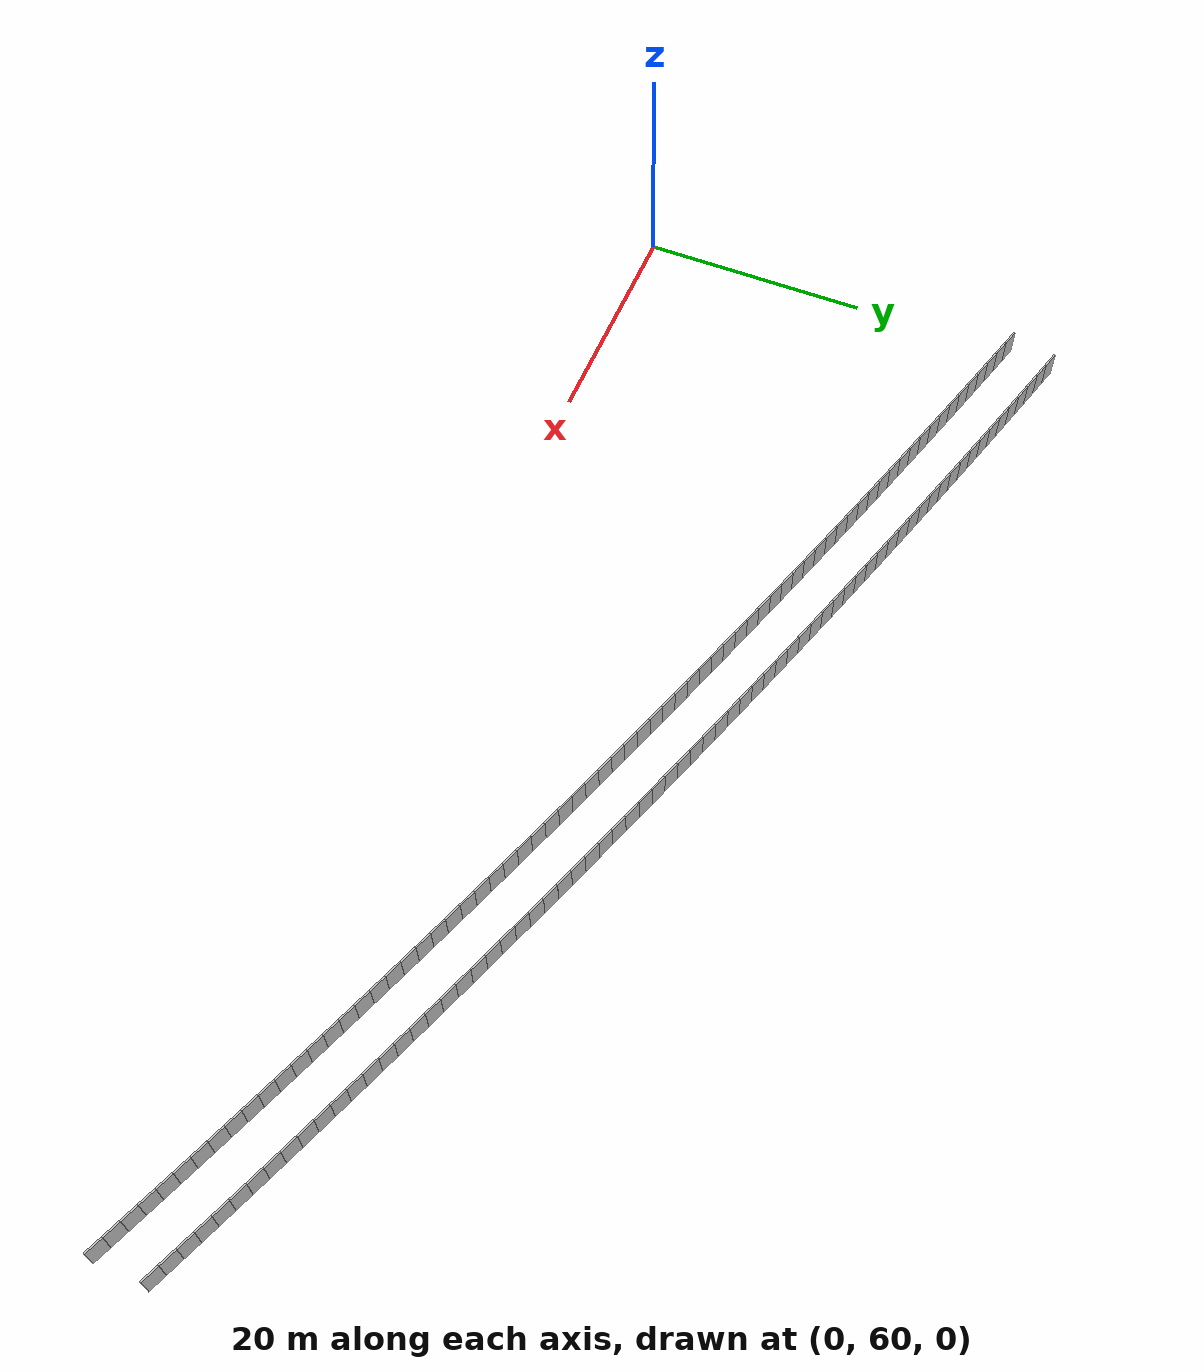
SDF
<?xml version="1.0" ?>
<sdf version="1.6">
  <model name="sps_1622">
    <pose frame="">0 0 0 0 -0 0</pose>
    <static>1</static>
    <self_collide>0</self_collide>
    <allow_auto_disable>0</allow_auto_disable>
    <link name="Wall10707">
      <kinematic>0</kinematic>
      <gravity>1</gravity>
      <self_collide>0</self_collide>
      <collision name="collision">
        <geometry>
          <box>
            <size>1.49636 0.15 2.5</size>
          </box>
        </geometry>
        <pose frame="">0 0 0 0 -0 0</pose>
      </collision>
      <visual name="visual">
        <geometry>
          <box>
            <size>1.49636 0.15 2.5</size>
          </box>
        </geometry>
        <pose frame="">0 0 0 0 -0 0</pose>
        <cast_shadows>1</cast_shadows>
        <transparency>0.0</transparency>
      </visual>
      <pose frame="">99.1837 59.711 1.25 0 -0 2.75123</pose>
    </link>
    <link name="Wall10708">
      <kinematic>0</kinematic>
      <gravity>1</gravity>
      <self_collide>0</self_collide>
      <collision name="collision">
        <geometry>
          <box>
            <size>1.49665 0.15 2.5</size>
          </box>
        </geometry>
        <pose frame="">0 0 0 0 -0 0</pose>
      </collision>
      <visual name="visual">
        <geometry>
          <box>
            <size>1.49665 0.15 2.5</size>
          </box>
        </geometry>
        <pose frame="">0 0 0 0 -0 0</pose>
        <cast_shadows>1</cast_shadows>
        <transparency>0.0</transparency>
      </visual>
      <pose frame="">97.7993 60.2793 1.25 0 -0 2.7529</pose>
    </link>
    <link name="Wall10709">
      <kinematic>0</kinematic>
      <gravity>1</gravity>
      <self_collide>0</self_collide>
      <collision name="collision">
        <geometry>
          <box>
            <size>1.49656 0.15 2.5</size>
          </box>
        </geometry>
        <pose frame="">0 0 0 0 -0 0</pose>
      </collision>
      <visual name="visual">
        <geometry>
          <box>
            <size>1.49656 0.15 2.5</size>
          </box>
        </geometry>
        <pose frame="">0 0 0 0 -0 0</pose>
        <cast_shadows>1</cast_shadows>
        <transparency>0.0</transparency>
      </visual>
      <pose frame="">96.4139 60.8454 1.25 0 -0 2.75446</pose>
    </link>
    <link name="Wall10710">
      <kinematic>0</kinematic>
      <gravity>1</gravity>
      <self_collide>0</self_collide>
      <collision name="collision">
        <geometry>
          <box>
            <size>1.49653 0.15 2.5</size>
          </box>
        </geometry>
        <pose frame="">0 0 0 0 -0 0</pose>
      </collision>
      <visual name="visual">
        <geometry>
          <box>
            <size>1.49653 0.15 2.5</size>
          </box>
        </geometry>
        <pose frame="">0 0 0 0 -0 0</pose>
        <cast_shadows>1</cast_shadows>
        <transparency>0.0</transparency>
      </visual>
      <pose frame="">95.0277 61.4094 1.25 0 -0 2.75591</pose>
    </link>
    <link name="Wall10711">
      <kinematic>0</kinematic>
      <gravity>1</gravity>
      <self_collide>0</self_collide>
      <collision name="collision">
        <geometry>
          <box>
            <size>1.49637 0.15 2.5</size>
          </box>
        </geometry>
        <pose frame="">0 0 0 0 -0 0</pose>
      </collision>
      <visual name="visual">
        <geometry>
          <box>
            <size>1.49637 0.15 2.5</size>
          </box>
        </geometry>
        <pose frame="">0 0 0 0 -0 0</pose>
        <cast_shadows>1</cast_shadows>
        <transparency>0.0</transparency>
      </visual>
      <pose frame="">93.6407 61.9712 1.25 0 -0 2.75758</pose>
    </link>
    <link name="Wall10712">
      <kinematic>0</kinematic>
      <gravity>1</gravity>
      <self_collide>0</self_collide>
      <collision name="collision">
        <geometry>
          <box>
            <size>1.49668 0.15 2.5</size>
          </box>
        </geometry>
        <pose frame="">0 0 0 0 -0 0</pose>
      </collision>
      <visual name="visual">
        <geometry>
          <box>
            <size>1.49668 0.15 2.5</size>
          </box>
        </geometry>
        <pose frame="">0 0 0 0 -0 0</pose>
        <cast_shadows>1</cast_shadows>
        <transparency>0.0</transparency>
      </visual>
      <pose frame="">92.2527 62.5307 1.25 0 -0 2.75925</pose>
    </link>
    <link name="Wall10713">
      <kinematic>0</kinematic>
      <gravity>1</gravity>
      <self_collide>0</self_collide>
      <collision name="collision">
        <geometry>
          <box>
            <size>1.49638 0.15 2.5</size>
          </box>
        </geometry>
        <pose frame="">0 0 0 0 -0 0</pose>
      </collision>
      <visual name="visual">
        <geometry>
          <box>
            <size>1.49638 0.15 2.5</size>
          </box>
        </geometry>
        <pose frame="">0 0 0 0 -0 0</pose>
        <cast_shadows>1</cast_shadows>
        <transparency>0.0</transparency>
      </visual>
      <pose frame="">90.8639 63.088 1.25 0 -0 2.76075</pose>
    </link>
    <link name="Wall10714">
      <kinematic>0</kinematic>
      <gravity>1</gravity>
      <self_collide>0</self_collide>
      <collision name="collision">
        <geometry>
          <box>
            <size>1.49652 0.15 2.5</size>
          </box>
        </geometry>
        <pose frame="">0 0 0 0 -0 0</pose>
      </collision>
      <visual name="visual">
        <geometry>
          <box>
            <size>1.49652 0.15 2.5</size>
          </box>
        </geometry>
        <pose frame="">0 0 0 0 -0 0</pose>
        <cast_shadows>1</cast_shadows>
        <transparency>0.0</transparency>
      </visual>
      <pose frame="">89.4742 63.6431 1.25 0 -0 2.76237</pose>
    </link>
    <link name="Wall10715">
      <kinematic>0</kinematic>
      <gravity>1</gravity>
      <self_collide>0</self_collide>
      <collision name="collision">
        <geometry>
          <box>
            <size>1.49652 0.15 2.5</size>
          </box>
        </geometry>
        <pose frame="">0 0 0 0 -0 0</pose>
      </collision>
      <visual name="visual">
        <geometry>
          <box>
            <size>1.49652 0.15 2.5</size>
          </box>
        </geometry>
        <pose frame="">0 0 0 0 -0 0</pose>
        <cast_shadows>1</cast_shadows>
        <transparency>0.0</transparency>
      </visual>
      <pose frame="">88.0836 64.1961 1.25 0 -0 2.76381</pose>
    </link>
    <link name="Wall10716">
      <kinematic>0</kinematic>
      <gravity>1</gravity>
      <self_collide>0</self_collide>
      <collision name="collision">
        <geometry>
          <box>
            <size>1.49641 0.15 2.5</size>
          </box>
        </geometry>
        <pose frame="">0 0 0 0 -0 0</pose>
      </collision>
      <visual name="visual">
        <geometry>
          <box>
            <size>1.49641 0.15 2.5</size>
          </box>
        </geometry>
        <pose frame="">0 0 0 0 -0 0</pose>
        <cast_shadows>1</cast_shadows>
        <transparency>0.0</transparency>
      </visual>
      <pose frame="">86.6922 64.7469 1.25 0 -0 2.76554</pose>
    </link>
    <link name="Wall10717">
      <kinematic>0</kinematic>
      <gravity>1</gravity>
      <self_collide>0</self_collide>
      <collision name="collision">
        <geometry>
          <box>
            <size>1.49678 0.15 2.5</size>
          </box>
        </geometry>
        <pose frame="">0 0 0 0 -0 0</pose>
      </collision>
      <visual name="visual">
        <geometry>
          <box>
            <size>1.49678 0.15 2.5</size>
          </box>
        </geometry>
        <pose frame="">0 0 0 0 -0 0</pose>
        <cast_shadows>1</cast_shadows>
        <transparency>0.0</transparency>
      </visual>
      <pose frame="">85.2997 65.2955 1.25 0 -0 2.76704</pose>
    </link>
    <link name="Wall10718">
      <kinematic>0</kinematic>
      <gravity>1</gravity>
      <self_collide>0</self_collide>
      <collision name="collision">
        <geometry>
          <box>
            <size>1.49642 0.15 2.5</size>
          </box>
        </geometry>
        <pose frame="">0 0 0 0 -0 0</pose>
      </collision>
      <visual name="visual">
        <geometry>
          <box>
            <size>1.49642 0.15 2.5</size>
          </box>
        </geometry>
        <pose frame="">0 0 0 0 -0 0</pose>
        <cast_shadows>1</cast_shadows>
        <transparency>0.0</transparency>
      </visual>
      <pose frame="">83.9065 65.8419 1.25 0 -0 2.76865</pose>
    </link>
    <link name="Wall10719">
      <kinematic>0</kinematic>
      <gravity>1</gravity>
      <self_collide>0</self_collide>
      <collision name="collision">
        <geometry>
          <box>
            <size>1.49663 0.15 2.5</size>
          </box>
        </geometry>
        <pose frame="">0 0 0 0 -0 0</pose>
      </collision>
      <visual name="visual">
        <geometry>
          <box>
            <size>1.49663 0.15 2.5</size>
          </box>
        </geometry>
        <pose frame="">0 0 0 0 -0 0</pose>
        <cast_shadows>1</cast_shadows>
        <transparency>0.0</transparency>
      </visual>
      <pose frame="">82.5124 66.3861 1.25 0 -0 2.7702</pose>
    </link>
    <link name="Wall10720">
      <kinematic>0</kinematic>
      <gravity>1</gravity>
      <self_collide>0</self_collide>
      <collision name="collision">
        <geometry>
          <box>
            <size>1.49659 0.15 2.5</size>
          </box>
        </geometry>
        <pose frame="">0 0 0 0 -0 0</pose>
      </collision>
      <visual name="visual">
        <geometry>
          <box>
            <size>1.49659 0.15 2.5</size>
          </box>
        </geometry>
        <pose frame="">0 0 0 0 -0 0</pose>
        <cast_shadows>1</cast_shadows>
        <transparency>0.0</transparency>
      </visual>
      <pose frame="">81.1174 66.9281 1.25 0 -0 2.77185</pose>
    </link>
    <link name="Wall10721">
      <kinematic>0</kinematic>
      <gravity>1</gravity>
      <self_collide>0</self_collide>
      <collision name="collision">
        <geometry>
          <box>
            <size>1.49628 0.15 2.5</size>
          </box>
        </geometry>
        <pose frame="">0 0 0 0 -0 0</pose>
      </collision>
      <visual name="visual">
        <geometry>
          <box>
            <size>1.49628 0.15 2.5</size>
          </box>
        </geometry>
        <pose frame="">0 0 0 0 -0 0</pose>
        <cast_shadows>1</cast_shadows>
        <transparency>0.0</transparency>
      </visual>
      <pose frame="">79.7216 67.4678 1.25 0 -0 2.77339</pose>
    </link>
    <link name="Wall10722">
      <kinematic>0</kinematic>
      <gravity>1</gravity>
      <self_collide>0</self_collide>
      <collision name="collision">
        <geometry>
          <box>
            <size>1.49657 0.15 2.5</size>
          </box>
        </geometry>
        <pose frame="">0 0 0 0 -0 0</pose>
      </collision>
      <visual name="visual">
        <geometry>
          <box>
            <size>1.49657 0.15 2.5</size>
          </box>
        </geometry>
        <pose frame="">0 0 0 0 -0 0</pose>
        <cast_shadows>1</cast_shadows>
        <transparency>0.0</transparency>
      </visual>
      <pose frame="">78.325 68.0052 1.25 0 -0 2.77517</pose>
    </link>
    <link name="Wall10723">
      <kinematic>0</kinematic>
      <gravity>1</gravity>
      <self_collide>0</self_collide>
      <collision name="collision">
        <geometry>
          <box>
            <size>1.49638 0.15 2.5</size>
          </box>
        </geometry>
        <pose frame="">0 0 0 0 -0 0</pose>
      </collision>
      <visual name="visual">
        <geometry>
          <box>
            <size>1.49638 0.15 2.5</size>
          </box>
        </geometry>
        <pose frame="">0 0 0 0 -0 0</pose>
        <cast_shadows>1</cast_shadows>
        <transparency>0.0</transparency>
      </visual>
      <pose frame="">76.9275 68.5404 1.25 0 -0 2.77652</pose>
    </link>
    <link name="Wall10724">
      <kinematic>0</kinematic>
      <gravity>1</gravity>
      <self_collide>0</self_collide>
      <collision name="collision">
        <geometry>
          <box>
            <size>1.49655 0.15 2.5</size>
          </box>
        </geometry>
        <pose frame="">0 0 0 0 -0 0</pose>
      </collision>
      <visual name="visual">
        <geometry>
          <box>
            <size>1.49655 0.15 2.5</size>
          </box>
        </geometry>
        <pose frame="">0 0 0 0 -0 0</pose>
        <cast_shadows>1</cast_shadows>
        <transparency>0.0</transparency>
      </visual>
      <pose frame="">75.5293 69.0735 1.25 0 -0 2.77817</pose>
    </link>
    <link name="Wall10725">
      <kinematic>0</kinematic>
      <gravity>1</gravity>
      <self_collide>0</self_collide>
      <collision name="collision">
        <geometry>
          <box>
            <size>1.49645 0.15 2.5</size>
          </box>
        </geometry>
        <pose frame="">0 0 0 0 -0 0</pose>
      </collision>
      <visual name="visual">
        <geometry>
          <box>
            <size>1.49645 0.15 2.5</size>
          </box>
        </geometry>
        <pose frame="">0 0 0 0 -0 0</pose>
        <cast_shadows>1</cast_shadows>
        <transparency>0.0</transparency>
      </visual>
      <pose frame="">74.1301 69.6043 1.25 0 -0 2.77985</pose>
    </link>
    <link name="Wall10726">
      <kinematic>0</kinematic>
      <gravity>1</gravity>
      <self_collide>0</self_collide>
      <collision name="collision">
        <geometry>
          <box>
            <size>1.49665 0.15 2.5</size>
          </box>
        </geometry>
        <pose frame="">0 0 0 0 -0 0</pose>
      </collision>
      <visual name="visual">
        <geometry>
          <box>
            <size>1.49665 0.15 2.5</size>
          </box>
        </geometry>
        <pose frame="">0 0 0 0 -0 0</pose>
        <cast_shadows>1</cast_shadows>
        <transparency>0.0</transparency>
      </visual>
      <pose frame="">72.73 70.1329 1.25 0 -0 2.78134</pose>
    </link>
    <link name="Wall10727">
      <kinematic>0</kinematic>
      <gravity>1</gravity>
      <self_collide>0</self_collide>
      <collision name="collision">
        <geometry>
          <box>
            <size>1.4965 0.15 2.5</size>
          </box>
        </geometry>
        <pose frame="">0 0 0 0 -0 0</pose>
      </collision>
      <visual name="visual">
        <geometry>
          <box>
            <size>1.4965 0.15 2.5</size>
          </box>
        </geometry>
        <pose frame="">0 0 0 0 -0 0</pose>
        <cast_shadows>1</cast_shadows>
        <transparency>0.0</transparency>
      </visual>
      <pose frame="">71.3291 70.6594 1.25 0 -0 2.78287</pose>
    </link>
    <link name="Wall10728">
      <kinematic>0</kinematic>
      <gravity>1</gravity>
      <self_collide>0</self_collide>
      <collision name="collision">
        <geometry>
          <box>
            <size>1.49636 0.15 2.5</size>
          </box>
        </geometry>
        <pose frame="">0 0 0 0 -0 0</pose>
      </collision>
      <visual name="visual">
        <geometry>
          <box>
            <size>1.49636 0.15 2.5</size>
          </box>
        </geometry>
        <pose frame="">0 0 0 0 -0 0</pose>
        <cast_shadows>1</cast_shadows>
        <transparency>0.0</transparency>
      </visual>
      <pose frame="">69.9275 71.1836 1.25 0 -0 2.78453</pose>
    </link>
    <link name="Wall10729">
      <kinematic>0</kinematic>
      <gravity>1</gravity>
      <self_collide>0</self_collide>
      <collision name="collision">
        <geometry>
          <box>
            <size>1.49663 0.15 2.5</size>
          </box>
        </geometry>
        <pose frame="">0 0 0 0 -0 0</pose>
      </collision>
      <visual name="visual">
        <geometry>
          <box>
            <size>1.49663 0.15 2.5</size>
          </box>
        </geometry>
        <pose frame="">0 0 0 0 -0 0</pose>
        <cast_shadows>1</cast_shadows>
        <transparency>0.0</transparency>
      </visual>
      <pose frame="">68.525 71.7056 1.25 0 -0 2.78603</pose>
    </link>
    <link name="Wall10730">
      <kinematic>0</kinematic>
      <gravity>1</gravity>
      <self_collide>0</self_collide>
      <collision name="collision">
        <geometry>
          <box>
            <size>1.49654 0.15 2.5</size>
          </box>
        </geometry>
        <pose frame="">0 0 0 0 -0 0</pose>
      </collision>
      <visual name="visual">
        <geometry>
          <box>
            <size>1.49654 0.15 2.5</size>
          </box>
        </geometry>
        <pose frame="">0 0 0 0 -0 0</pose>
        <cast_shadows>1</cast_shadows>
        <transparency>0.0</transparency>
      </visual>
      <pose frame="">67.1215 72.2254 1.25 0 -0 2.78771</pose>
    </link>
    <link name="Wall10731">
      <kinematic>0</kinematic>
      <gravity>1</gravity>
      <self_collide>0</self_collide>
      <collision name="collision">
        <geometry>
          <box>
            <size>1.49653 0.15 2.5</size>
          </box>
        </geometry>
        <pose frame="">0 0 0 0 -0 0</pose>
      </collision>
      <visual name="visual">
        <geometry>
          <box>
            <size>1.49653 0.15 2.5</size>
          </box>
        </geometry>
        <pose frame="">0 0 0 0 -0 0</pose>
        <cast_shadows>1</cast_shadows>
        <transparency>0.0</transparency>
      </visual>
      <pose frame="">65.7173 72.7429 1.25 0 -0 2.78927</pose>
    </link>
    <link name="Wall10732">
      <kinematic>0</kinematic>
      <gravity>1</gravity>
      <self_collide>0</self_collide>
      <collision name="collision">
        <geometry>
          <box>
            <size>1.49649 0.15 2.5</size>
          </box>
        </geometry>
        <pose frame="">0 0 0 0 -0 0</pose>
      </collision>
      <visual name="visual">
        <geometry>
          <box>
            <size>1.49649 0.15 2.5</size>
          </box>
        </geometry>
        <pose frame="">0 0 0 0 -0 0</pose>
        <cast_shadows>1</cast_shadows>
        <transparency>0.0</transparency>
      </visual>
      <pose frame="">64.3123 73.2582 1.25 0 -0 2.79087</pose>
    </link>
    <link name="Wall10733">
      <kinematic>0</kinematic>
      <gravity>1</gravity>
      <self_collide>0</self_collide>
      <collision name="collision">
        <geometry>
          <box>
            <size>1.49645 0.15 2.5</size>
          </box>
        </geometry>
        <pose frame="">0 0 0 0 -0 0</pose>
      </collision>
      <visual name="visual">
        <geometry>
          <box>
            <size>1.49645 0.15 2.5</size>
          </box>
        </geometry>
        <pose frame="">0 0 0 0 -0 0</pose>
        <cast_shadows>1</cast_shadows>
        <transparency>0.0</transparency>
      </visual>
      <pose frame="">62.9065 73.7712 1.25 0 -0 2.79251</pose>
    </link>
    <link name="Wall10734">
      <kinematic>0</kinematic>
      <gravity>1</gravity>
      <self_collide>0</self_collide>
      <collision name="collision">
        <geometry>
          <box>
            <size>1.49671 0.15 2.5</size>
          </box>
        </geometry>
        <pose frame="">0 0 0 0 -0 0</pose>
      </collision>
      <visual name="visual">
        <geometry>
          <box>
            <size>1.49671 0.15 2.5</size>
          </box>
        </geometry>
        <pose frame="">0 0 0 0 -0 0</pose>
        <cast_shadows>1</cast_shadows>
        <transparency>0.0</transparency>
      </visual>
      <pose frame="">61.4998 74.282 1.25 0 -0 2.79405</pose>
    </link>
    <link name="Wall10735">
      <kinematic>0</kinematic>
      <gravity>1</gravity>
      <self_collide>0</self_collide>
      <collision name="collision">
        <geometry>
          <box>
            <size>1.49625 0.15 2.5</size>
          </box>
        </geometry>
        <pose frame="">0 0 0 0 -0 0</pose>
      </collision>
      <visual name="visual">
        <geometry>
          <box>
            <size>1.49625 0.15 2.5</size>
          </box>
        </geometry>
        <pose frame="">0 0 0 0 -0 0</pose>
        <cast_shadows>1</cast_shadows>
        <transparency>0.0</transparency>
      </visual>
      <pose frame="">60.0924 74.7906 1.25 0 -0 2.79563</pose>
    </link>
    <link name="Wall10736">
      <kinematic>0</kinematic>
      <gravity>1</gravity>
      <self_collide>0</self_collide>
      <collision name="collision">
        <geometry>
          <box>
            <size>1.49651 0.15 2.5</size>
          </box>
        </geometry>
        <pose frame="">0 0 0 0 -0 0</pose>
      </collision>
      <visual name="visual">
        <geometry>
          <box>
            <size>1.49651 0.15 2.5</size>
          </box>
        </geometry>
        <pose frame="">0 0 0 0 -0 0</pose>
        <cast_shadows>1</cast_shadows>
        <transparency>0.0</transparency>
      </visual>
      <pose frame="">58.6843 75.297 1.25 0 -0 2.79708</pose>
    </link>
    <link name="Wall10737">
      <kinematic>0</kinematic>
      <gravity>1</gravity>
      <self_collide>0</self_collide>
      <collision name="collision">
        <geometry>
          <box>
            <size>1.49649 0.15 2.5</size>
          </box>
        </geometry>
        <pose frame="">0 0 0 0 -0 0</pose>
      </collision>
      <visual name="visual">
        <geometry>
          <box>
            <size>1.49649 0.15 2.5</size>
          </box>
        </geometry>
        <pose frame="">0 0 0 0 -0 0</pose>
        <cast_shadows>1</cast_shadows>
        <transparency>0.0</transparency>
      </visual>
      <pose frame="">57.2754 75.8012 1.25 0 -0 2.7988</pose>
    </link>
    <link name="Wall10738">
      <kinematic>0</kinematic>
      <gravity>1</gravity>
      <self_collide>0</self_collide>
      <collision name="collision">
        <geometry>
          <box>
            <size>1.49667 0.15 2.5</size>
          </box>
        </geometry>
        <pose frame="">0 0 0 0 -0 0</pose>
      </collision>
      <visual name="visual">
        <geometry>
          <box>
            <size>1.49667 0.15 2.5</size>
          </box>
        </geometry>
        <pose frame="">0 0 0 0 -0 0</pose>
        <cast_shadows>1</cast_shadows>
        <transparency>0.0</transparency>
      </visual>
      <pose frame="">55.8654 76.3031 1.25 0 -0 2.80041</pose>
    </link>
    <link name="Wall10739">
      <kinematic>0</kinematic>
      <gravity>1</gravity>
      <self_collide>0</self_collide>
      <collision name="collision">
        <geometry>
          <box>
            <size>1.49651 0.15 2.5</size>
          </box>
        </geometry>
        <pose frame="">0 0 0 0 -0 0</pose>
      </collision>
      <visual name="visual">
        <geometry>
          <box>
            <size>1.49651 0.15 2.5</size>
          </box>
        </geometry>
        <pose frame="">0 0 0 0 -0 0</pose>
        <cast_shadows>1</cast_shadows>
        <transparency>0.0</transparency>
      </visual>
      <pose frame="">54.4547 76.8028 1.25 0 -0 2.80193</pose>
    </link>
    <link name="Wall10740">
      <kinematic>0</kinematic>
      <gravity>1</gravity>
      <self_collide>0</self_collide>
      <collision name="collision">
        <geometry>
          <box>
            <size>1.49647 0.15 2.5</size>
          </box>
        </geometry>
        <pose frame="">0 0 0 0 -0 0</pose>
      </collision>
      <visual name="visual">
        <geometry>
          <box>
            <size>1.49647 0.15 2.5</size>
          </box>
        </geometry>
        <pose frame="">0 0 0 0 -0 0</pose>
        <cast_shadows>1</cast_shadows>
        <transparency>0.0</transparency>
      </visual>
      <pose frame="">53.0434 77.3003 1.25 0 -0 2.80347</pose>
    </link>
    <link name="Wall10741">
      <kinematic>0</kinematic>
      <gravity>1</gravity>
      <self_collide>0</self_collide>
      <collision name="collision">
        <geometry>
          <box>
            <size>1.49655 0.15 2.5</size>
          </box>
        </geometry>
        <pose frame="">0 0 0 0 -0 0</pose>
      </collision>
      <visual name="visual">
        <geometry>
          <box>
            <size>1.49655 0.15 2.5</size>
          </box>
        </geometry>
        <pose frame="">0 0 0 0 -0 0</pose>
        <cast_shadows>1</cast_shadows>
        <transparency>0.0</transparency>
      </visual>
      <pose frame="">51.6312 77.7955 1.25 0 -0 2.80518</pose>
    </link>
    <link name="Wall10742">
      <kinematic>0</kinematic>
      <gravity>1</gravity>
      <self_collide>0</self_collide>
      <collision name="collision">
        <geometry>
          <box>
            <size>1.49652 0.15 2.5</size>
          </box>
        </geometry>
        <pose frame="">0 0 0 0 -0 0</pose>
      </collision>
      <visual name="visual">
        <geometry>
          <box>
            <size>1.49652 0.15 2.5</size>
          </box>
        </geometry>
        <pose frame="">0 0 0 0 -0 0</pose>
        <cast_shadows>1</cast_shadows>
        <transparency>0.0</transparency>
      </visual>
      <pose frame="">50.2181 78.2884 1.25 0 -0 2.80673</pose>
    </link>
    <link name="Wall10743">
      <kinematic>0</kinematic>
      <gravity>1</gravity>
      <self_collide>0</self_collide>
      <collision name="collision">
        <geometry>
          <box>
            <size>1.49653 0.15 2.5</size>
          </box>
        </geometry>
        <pose frame="">0 0 0 0 -0 0</pose>
      </collision>
      <visual name="visual">
        <geometry>
          <box>
            <size>1.49653 0.15 2.5</size>
          </box>
        </geometry>
        <pose frame="">0 0 0 0 -0 0</pose>
        <cast_shadows>1</cast_shadows>
        <transparency>0.0</transparency>
      </visual>
      <pose frame="">48.8043 78.7791 1.25 0 -0 2.80832</pose>
    </link>
    <link name="Wall10744">
      <kinematic>0</kinematic>
      <gravity>1</gravity>
      <self_collide>0</self_collide>
      <collision name="collision">
        <geometry>
          <box>
            <size>1.49641 0.15 2.5</size>
          </box>
        </geometry>
        <pose frame="">0 0 0 0 -0 0</pose>
      </collision>
      <visual name="visual">
        <geometry>
          <box>
            <size>1.49641 0.15 2.5</size>
          </box>
        </geometry>
        <pose frame="">0 0 0 0 -0 0</pose>
        <cast_shadows>1</cast_shadows>
        <transparency>0.0</transparency>
      </visual>
      <pose frame="">47.3899 79.2676 1.25 0 -0 2.80981</pose>
    </link>
    <link name="Wall10745">
      <kinematic>0</kinematic>
      <gravity>1</gravity>
      <self_collide>0</self_collide>
      <collision name="collision">
        <geometry>
          <box>
            <size>1.4966 0.15 2.5</size>
          </box>
        </geometry>
        <pose frame="">0 0 0 0 -0 0</pose>
      </collision>
      <visual name="visual">
        <geometry>
          <box>
            <size>1.4966 0.15 2.5</size>
          </box>
        </geometry>
        <pose frame="">0 0 0 0 -0 0</pose>
        <cast_shadows>1</cast_shadows>
        <transparency>0.0</transparency>
      </visual>
      <pose frame="">45.9746 79.7539 1.25 0 -0 2.81145</pose>
    </link>
    <link name="Wall10746">
      <kinematic>0</kinematic>
      <gravity>1</gravity>
      <self_collide>0</self_collide>
      <collision name="collision">
        <geometry>
          <box>
            <size>1.49654 0.15 2.5</size>
          </box>
        </geometry>
        <pose frame="">0 0 0 0 -0 0</pose>
      </collision>
      <visual name="visual">
        <geometry>
          <box>
            <size>1.49654 0.15 2.5</size>
          </box>
        </geometry>
        <pose frame="">0 0 0 0 -0 0</pose>
        <cast_shadows>1</cast_shadows>
        <transparency>0.0</transparency>
      </visual>
      <pose frame="">44.5585 80.238 1.25 0 -0 2.81294</pose>
    </link>
    <link name="Wall10747">
      <kinematic>0</kinematic>
      <gravity>1</gravity>
      <self_collide>0</self_collide>
      <collision name="collision">
        <geometry>
          <box>
            <size>1.49662 0.15 2.5</size>
          </box>
        </geometry>
        <pose frame="">0 0 0 0 -0 0</pose>
      </collision>
      <visual name="visual">
        <geometry>
          <box>
            <size>1.49662 0.15 2.5</size>
          </box>
        </geometry>
        <pose frame="">0 0 0 0 -0 0</pose>
        <cast_shadows>1</cast_shadows>
        <transparency>0.0</transparency>
      </visual>
      <pose frame="">43.1416 80.7198 1.25 0 -0 2.81468</pose>
    </link>
    <link name="Wall10748">
      <kinematic>0</kinematic>
      <gravity>1</gravity>
      <self_collide>0</self_collide>
      <collision name="collision">
        <geometry>
          <box>
            <size>1.49638 0.15 2.5</size>
          </box>
        </geometry>
        <pose frame="">0 0 0 0 -0 0</pose>
      </collision>
      <visual name="visual">
        <geometry>
          <box>
            <size>1.49638 0.15 2.5</size>
          </box>
        </geometry>
        <pose frame="">0 0 0 0 -0 0</pose>
        <cast_shadows>1</cast_shadows>
        <transparency>0.0</transparency>
      </visual>
      <pose frame="">41.724 81.1993 1.25 0 -0 2.81618</pose>
    </link>
    <link name="Wall10749">
      <kinematic>0</kinematic>
      <gravity>1</gravity>
      <self_collide>0</self_collide>
      <collision name="collision">
        <geometry>
          <box>
            <size>1.49649 0.15 2.5</size>
          </box>
        </geometry>
        <pose frame="">0 0 0 0 -0 0</pose>
      </collision>
      <visual name="visual">
        <geometry>
          <box>
            <size>1.49649 0.15 2.5</size>
          </box>
        </geometry>
        <pose frame="">0 0 0 0 -0 0</pose>
        <cast_shadows>1</cast_shadows>
        <transparency>0.0</transparency>
      </visual>
      <pose frame="">40.3057 81.6765 1.25 0 -0 2.81788</pose>
    </link>
    <link name="Wall10750">
      <kinematic>0</kinematic>
      <gravity>1</gravity>
      <self_collide>0</self_collide>
      <collision name="collision">
        <geometry>
          <box>
            <size>1.49648 0.15 2.5</size>
          </box>
        </geometry>
        <pose frame="">0 0 0 0 -0 0</pose>
      </collision>
      <visual name="visual">
        <geometry>
          <box>
            <size>1.49648 0.15 2.5</size>
          </box>
        </geometry>
        <pose frame="">0 0 0 0 -0 0</pose>
        <cast_shadows>1</cast_shadows>
        <transparency>0.0</transparency>
      </visual>
      <pose frame="">38.8866 82.1515 1.25 0 -0 2.8193</pose>
    </link>
    <link name="Wall10751">
      <kinematic>0</kinematic>
      <gravity>1</gravity>
      <self_collide>0</self_collide>
      <collision name="collision">
        <geometry>
          <box>
            <size>1.49672 0.15 2.5</size>
          </box>
        </geometry>
        <pose frame="">0 0 0 0 -0 0</pose>
      </collision>
      <visual name="visual">
        <geometry>
          <box>
            <size>1.49672 0.15 2.5</size>
          </box>
        </geometry>
        <pose frame="">0 0 0 0 -0 0</pose>
        <cast_shadows>1</cast_shadows>
        <transparency>0.0</transparency>
      </visual>
      <pose frame="">37.4666 82.6244 1.25 0 -0 2.8209</pose>
    </link>
    <link name="Wall10752">
      <kinematic>0</kinematic>
      <gravity>1</gravity>
      <self_collide>0</self_collide>
      <collision name="collision">
        <geometry>
          <box>
            <size>1.4963 0.15 2.5</size>
          </box>
        </geometry>
        <pose frame="">0 0 0 0 -0 0</pose>
      </collision>
      <visual name="visual">
        <geometry>
          <box>
            <size>1.4963 0.15 2.5</size>
          </box>
        </geometry>
        <pose frame="">0 0 0 0 -0 0</pose>
        <cast_shadows>1</cast_shadows>
        <transparency>0.0</transparency>
      </visual>
      <pose frame="">36.046 83.095 1.25 0 -0 2.82253</pose>
    </link>
    <link name="Wall10753">
      <kinematic>0</kinematic>
      <gravity>1</gravity>
      <self_collide>0</self_collide>
      <collision name="collision">
        <geometry>
          <box>
            <size>1.49656 0.15 2.5</size>
          </box>
        </geometry>
        <pose frame="">0 0 0 0 -0 0</pose>
      </collision>
      <visual name="visual">
        <geometry>
          <box>
            <size>1.49656 0.15 2.5</size>
          </box>
        </geometry>
        <pose frame="">0 0 0 0 -0 0</pose>
        <cast_shadows>1</cast_shadows>
        <transparency>0.0</transparency>
      </visual>
      <pose frame="">34.6247 83.5632 1.25 0 -0 2.82421</pose>
    </link>
    <link name="Wall10754">
      <kinematic>0</kinematic>
      <gravity>1</gravity>
      <self_collide>0</self_collide>
      <collision name="collision">
        <geometry>
          <box>
            <size>1.49643 0.15 2.5</size>
          </box>
        </geometry>
        <pose frame="">0 0 0 0 -0 0</pose>
      </collision>
      <visual name="visual">
        <geometry>
          <box>
            <size>1.49643 0.15 2.5</size>
          </box>
        </geometry>
        <pose frame="">0 0 0 0 -0 0</pose>
        <cast_shadows>1</cast_shadows>
        <transparency>0.0</transparency>
      </visual>
      <pose frame="">33.2027 84.0292 1.25 0 -0 2.82565</pose>
    </link>
    <link name="Wall10755">
      <kinematic>0</kinematic>
      <gravity>1</gravity>
      <self_collide>0</self_collide>
      <collision name="collision">
        <geometry>
          <box>
            <size>1.49653 0.15 2.5</size>
          </box>
        </geometry>
        <pose frame="">0 0 0 0 -0 0</pose>
      </collision>
      <visual name="visual">
        <geometry>
          <box>
            <size>1.49653 0.15 2.5</size>
          </box>
        </geometry>
        <pose frame="">0 0 0 0 -0 0</pose>
        <cast_shadows>1</cast_shadows>
        <transparency>0.0</transparency>
      </visual>
      <pose frame="">31.7799 84.493 1.25 0 -0 2.8273</pose>
    </link>
    <link name="Wall10756">
      <kinematic>0</kinematic>
      <gravity>1</gravity>
      <self_collide>0</self_collide>
      <collision name="collision">
        <geometry>
          <box>
            <size>1.49658 0.15 2.5</size>
          </box>
        </geometry>
        <pose frame="">0 0 0 0 -0 0</pose>
      </collision>
      <visual name="visual">
        <geometry>
          <box>
            <size>1.49658 0.15 2.5</size>
          </box>
        </geometry>
        <pose frame="">0 0 0 0 -0 0</pose>
        <cast_shadows>1</cast_shadows>
        <transparency>0.0</transparency>
      </visual>
      <pose frame="">30.3563 84.9545 1.25 0 -0 2.8289</pose>
    </link>
    <link name="Wall10757">
      <kinematic>0</kinematic>
      <gravity>1</gravity>
      <self_collide>0</self_collide>
      <collision name="collision">
        <geometry>
          <box>
            <size>1.49649 0.15 2.5</size>
          </box>
        </geometry>
        <pose frame="">0 0 0 0 -0 0</pose>
      </collision>
      <visual name="visual">
        <geometry>
          <box>
            <size>1.49649 0.15 2.5</size>
          </box>
        </geometry>
        <pose frame="">0 0 0 0 -0 0</pose>
        <cast_shadows>1</cast_shadows>
        <transparency>0.0</transparency>
      </visual>
      <pose frame="">28.9319 85.4138 1.25 0 -0 2.83042</pose>
    </link>
    <link name="Wall10758">
      <kinematic>0</kinematic>
      <gravity>1</gravity>
      <self_collide>0</self_collide>
      <collision name="collision">
        <geometry>
          <box>
            <size>1.49646 0.15 2.5</size>
          </box>
        </geometry>
        <pose frame="">0 0 0 0 -0 0</pose>
      </collision>
      <visual name="visual">
        <geometry>
          <box>
            <size>1.49646 0.15 2.5</size>
          </box>
        </geometry>
        <pose frame="">0 0 0 0 -0 0</pose>
        <cast_shadows>1</cast_shadows>
        <transparency>0.0</transparency>
      </visual>
      <pose frame="">27.5069 85.8708 1.25 0 -0 2.83208</pose>
    </link>
    <link name="Wall10759">
      <kinematic>0</kinematic>
      <gravity>1</gravity>
      <self_collide>0</self_collide>
      <collision name="collision">
        <geometry>
          <box>
            <size>1.49661 0.15 2.5</size>
          </box>
        </geometry>
        <pose frame="">0 0 0 0 -0 0</pose>
      </collision>
      <visual name="visual">
        <geometry>
          <box>
            <size>1.49661 0.15 2.5</size>
          </box>
        </geometry>
        <pose frame="">0 0 0 0 -0 0</pose>
        <cast_shadows>1</cast_shadows>
        <transparency>0.0</transparency>
      </visual>
      <pose frame="">26.0812 86.3255 1.25 0 -0 2.83365</pose>
    </link>
    <link name="Wall10760">
      <kinematic>0</kinematic>
      <gravity>1</gravity>
      <self_collide>0</self_collide>
      <collision name="collision">
        <geometry>
          <box>
            <size>1.49633 0.15 2.5</size>
          </box>
        </geometry>
        <pose frame="">0 0 0 0 -0 0</pose>
      </collision>
      <visual name="visual">
        <geometry>
          <box>
            <size>1.49633 0.15 2.5</size>
          </box>
        </geometry>
        <pose frame="">0 0 0 0 -0 0</pose>
        <cast_shadows>1</cast_shadows>
        <transparency>0.0</transparency>
      </visual>
      <pose frame="">24.6547 86.778 1.25 0 -0 2.83518</pose>
    </link>
    <link name="Wall10761">
      <kinematic>0</kinematic>
      <gravity>1</gravity>
      <self_collide>0</self_collide>
      <collision name="collision">
        <geometry>
          <box>
            <size>1.49656 0.15 2.5</size>
          </box>
        </geometry>
        <pose frame="">0 0 0 0 -0 0</pose>
      </collision>
      <visual name="visual">
        <geometry>
          <box>
            <size>1.49656 0.15 2.5</size>
          </box>
        </geometry>
        <pose frame="">0 0 0 0 -0 0</pose>
        <cast_shadows>1</cast_shadows>
        <transparency>0.0</transparency>
      </visual>
      <pose frame="">23.2277 87.2283 1.25 0 -0 2.83672</pose>
    </link>
    <link name="Wall10762">
      <kinematic>0</kinematic>
      <gravity>1</gravity>
      <self_collide>0</self_collide>
      <collision name="collision">
        <geometry>
          <box>
            <size>1.49647 0.15 2.5</size>
          </box>
        </geometry>
        <pose frame="">0 0 0 0 -0 0</pose>
      </collision>
      <visual name="visual">
        <geometry>
          <box>
            <size>1.49647 0.15 2.5</size>
          </box>
        </geometry>
        <pose frame="">0 0 0 0 -0 0</pose>
        <cast_shadows>1</cast_shadows>
        <transparency>0.0</transparency>
      </visual>
      <pose frame="">21.7998 87.6763 1.25 0 -0 2.83842</pose>
    </link>
    <link name="Wall10763">
      <kinematic>0</kinematic>
      <gravity>1</gravity>
      <self_collide>0</self_collide>
      <collision name="collision">
        <geometry>
          <box>
            <size>1.49659 0.15 2.5</size>
          </box>
        </geometry>
        <pose frame="">0 0 0 0 -0 0</pose>
      </collision>
      <visual name="visual">
        <geometry>
          <box>
            <size>1.49659 0.15 2.5</size>
          </box>
        </geometry>
        <pose frame="">0 0 0 0 -0 0</pose>
        <cast_shadows>1</cast_shadows>
        <transparency>0.0</transparency>
      </visual>
      <pose frame="">20.3711 88.122 1.25 0 -0 2.83994</pose>
    </link>
    <link name="Wall10764">
      <kinematic>0</kinematic>
      <gravity>1</gravity>
      <self_collide>0</self_collide>
      <collision name="collision">
        <geometry>
          <box>
            <size>1.49663 0.15 2.5</size>
          </box>
        </geometry>
        <pose frame="">0 0 0 0 -0 0</pose>
      </collision>
      <visual name="visual">
        <geometry>
          <box>
            <size>1.49663 0.15 2.5</size>
          </box>
        </geometry>
        <pose frame="">0 0 0 0 -0 0</pose>
        <cast_shadows>1</cast_shadows>
        <transparency>0.0</transparency>
      </visual>
      <pose frame="">18.9417 88.5654 1.25 0 -0 2.84165</pose>
    </link>
    <link name="Wall10765">
      <kinematic>0</kinematic>
      <gravity>1</gravity>
      <self_collide>0</self_collide>
      <collision name="collision">
        <geometry>
          <box>
            <size>1.49638 0.15 2.5</size>
          </box>
        </geometry>
        <pose frame="">0 0 0 0 -0 0</pose>
      </collision>
      <visual name="visual">
        <geometry>
          <box>
            <size>1.49638 0.15 2.5</size>
          </box>
        </geometry>
        <pose frame="">0 0 0 0 -0 0</pose>
        <cast_shadows>1</cast_shadows>
        <transparency>0.0</transparency>
      </visual>
      <pose frame="">17.5117 89.0066 1.25 0 -0 2.84301</pose>
    </link>
    <link name="Wall10766">
      <kinematic>0</kinematic>
      <gravity>1</gravity>
      <self_collide>0</self_collide>
      <collision name="collision">
        <geometry>
          <box>
            <size>1.49639 0.15 2.5</size>
          </box>
        </geometry>
        <pose frame="">0 0 0 0 -0 0</pose>
      </collision>
      <visual name="visual">
        <geometry>
          <box>
            <size>1.49639 0.15 2.5</size>
          </box>
        </geometry>
        <pose frame="">0 0 0 0 -0 0</pose>
        <cast_shadows>1</cast_shadows>
        <transparency>0.0</transparency>
      </visual>
      <pose frame="">16.0812 89.4455 1.25 0 -0 2.8448</pose>
    </link>
    <link name="Wall10767">
      <kinematic>0</kinematic>
      <gravity>1</gravity>
      <self_collide>0</self_collide>
      <collision name="collision">
        <geometry>
          <box>
            <size>1.4966 0.15 2.5</size>
          </box>
        </geometry>
        <pose frame="">0 0 0 0 -0 0</pose>
      </collision>
      <visual name="visual">
        <geometry>
          <box>
            <size>1.4966 0.15 2.5</size>
          </box>
        </geometry>
        <pose frame="">0 0 0 0 -0 0</pose>
        <cast_shadows>1</cast_shadows>
        <transparency>0.0</transparency>
      </visual>
      <pose frame="">14.6498 89.8821 1.25 0 -0 2.8463</pose>
    </link>
    <link name="Wall10768">
      <kinematic>0</kinematic>
      <gravity>1</gravity>
      <self_collide>0</self_collide>
      <collision name="collision">
        <geometry>
          <box>
            <size>1.49651 0.15 2.5</size>
          </box>
        </geometry>
        <pose frame="">0 0 0 0 -0 0</pose>
      </collision>
      <visual name="visual">
        <geometry>
          <box>
            <size>1.49651 0.15 2.5</size>
          </box>
        </geometry>
        <pose frame="">0 0 0 0 -0 0</pose>
        <cast_shadows>1</cast_shadows>
        <transparency>0.0</transparency>
      </visual>
      <pose frame="">13.2176 90.3165 1.25 0 -0 2.8479</pose>
    </link>
    <link name="Wall10769">
      <kinematic>0</kinematic>
      <gravity>1</gravity>
      <self_collide>0</self_collide>
      <collision name="collision">
        <geometry>
          <box>
            <size>1.49656 0.15 2.5</size>
          </box>
        </geometry>
        <pose frame="">0 0 0 0 -0 0</pose>
      </collision>
      <visual name="visual">
        <geometry>
          <box>
            <size>1.49656 0.15 2.5</size>
          </box>
        </geometry>
        <pose frame="">0 0 0 0 -0 0</pose>
        <cast_shadows>1</cast_shadows>
        <transparency>0.0</transparency>
      </visual>
      <pose frame="">11.7848 90.7486 1.25 0 -0 2.84948</pose>
    </link>
    <link name="Wall10770">
      <kinematic>0</kinematic>
      <gravity>1</gravity>
      <self_collide>0</self_collide>
      <collision name="collision">
        <geometry>
          <box>
            <size>1.49653 0.15 2.5</size>
          </box>
        </geometry>
        <pose frame="">0 0 0 0 -0 0</pose>
      </collision>
      <visual name="visual">
        <geometry>
          <box>
            <size>1.49653 0.15 2.5</size>
          </box>
        </geometry>
        <pose frame="">0 0 0 0 -0 0</pose>
        <cast_shadows>1</cast_shadows>
        <transparency>0.0</transparency>
      </visual>
      <pose frame="">10.3514 91.1785 1.25 0 -0 2.85097</pose>
    </link>
    <link name="Wall10771">
      <kinematic>0</kinematic>
      <gravity>1</gravity>
      <self_collide>0</self_collide>
      <collision name="collision">
        <geometry>
          <box>
            <size>1.49648 0.15 2.5</size>
          </box>
        </geometry>
        <pose frame="">0 0 0 0 -0 0</pose>
      </collision>
      <visual name="visual">
        <geometry>
          <box>
            <size>1.49648 0.15 2.5</size>
          </box>
        </geometry>
        <pose frame="">0 0 0 0 -0 0</pose>
        <cast_shadows>1</cast_shadows>
        <transparency>0.0</transparency>
      </visual>
      <pose frame="">8.91726 91.6061 1.25 0 -0 2.85266</pose>
    </link>
    <link name="Wall10772">
      <kinematic>0</kinematic>
      <gravity>1</gravity>
      <self_collide>0</self_collide>
      <collision name="collision">
        <geometry>
          <box>
            <size>1.49651 0.15 2.5</size>
          </box>
        </geometry>
        <pose frame="">0 0 0 0 -0 0</pose>
      </collision>
      <visual name="visual">
        <geometry>
          <box>
            <size>1.49651 0.15 2.5</size>
          </box>
        </geometry>
        <pose frame="">0 0 0 0 -0 0</pose>
        <cast_shadows>1</cast_shadows>
        <transparency>0.0</transparency>
      </visual>
      <pose frame="">7.48244 92.0313 1.25 0 -0 2.85432</pose>
    </link>
    <link name="Wall10773">
      <kinematic>0</kinematic>
      <gravity>1</gravity>
      <self_collide>0</self_collide>
      <collision name="collision">
        <geometry>
          <box>
            <size>1.49652 0.15 2.5</size>
          </box>
        </geometry>
        <pose frame="">0 0 0 0 -0 0</pose>
      </collision>
      <visual name="visual">
        <geometry>
          <box>
            <size>1.49652 0.15 2.5</size>
          </box>
        </geometry>
        <pose frame="">0 0 0 0 -0 0</pose>
        <cast_shadows>1</cast_shadows>
        <transparency>0.0</transparency>
      </visual>
      <pose frame="">6.04696 92.4543 1.25 0 -0 2.85573</pose>
    </link>
    <link name="Wall10774">
      <kinematic>0</kinematic>
      <gravity>1</gravity>
      <self_collide>0</self_collide>
      <collision name="collision">
        <geometry>
          <box>
            <size>1.49637 0.15 2.5</size>
          </box>
        </geometry>
        <pose frame="">0 0 0 0 -0 0</pose>
      </collision>
      <visual name="visual">
        <geometry>
          <box>
            <size>1.49637 0.15 2.5</size>
          </box>
        </geometry>
        <pose frame="">0 0 0 0 -0 0</pose>
        <cast_shadows>1</cast_shadows>
        <transparency>0.0</transparency>
      </visual>
      <pose frame="">4.61086 92.875 1.25 0 -0 2.85753</pose>
    </link>
    <link name="Wall10775">
      <kinematic>0</kinematic>
      <gravity>1</gravity>
      <self_collide>0</self_collide>
      <collision name="collision">
        <geometry>
          <box>
            <size>1.49659 0.15 2.5</size>
          </box>
        </geometry>
        <pose frame="">0 0 0 0 -0 0</pose>
      </collision>
      <visual name="visual">
        <geometry>
          <box>
            <size>1.49659 0.15 2.5</size>
          </box>
        </geometry>
        <pose frame="">0 0 0 0 -0 0</pose>
        <cast_shadows>1</cast_shadows>
        <transparency>0.0</transparency>
      </visual>
      <pose frame="">3.17406 93.2934 1.25 0 -0 2.85893</pose>
    </link>
    <link name="Wall10776">
      <kinematic>0</kinematic>
      <gravity>1</gravity>
      <self_collide>0</self_collide>
      <collision name="collision">
        <geometry>
          <box>
            <size>1.49649 0.15 2.5</size>
          </box>
        </geometry>
        <pose frame="">0 0 0 0 -0 0</pose>
      </collision>
      <visual name="visual">
        <geometry>
          <box>
            <size>1.49649 0.15 2.5</size>
          </box>
        </geometry>
        <pose frame="">0 0 0 0 -0 0</pose>
        <cast_shadows>1</cast_shadows>
        <transparency>0.0</transparency>
      </visual>
      <pose frame="">1.73656 93.7096 1.25 0 -0 2.86061</pose>
    </link>
    <link name="Wall10777">
      <kinematic>0</kinematic>
      <gravity>1</gravity>
      <self_collide>0</self_collide>
      <collision name="collision">
        <geometry>
          <box>
            <size>1.49654 0.15 2.5</size>
          </box>
        </geometry>
        <pose frame="">0 0 0 0 -0 0</pose>
      </collision>
      <visual name="visual">
        <geometry>
          <box>
            <size>1.49654 0.15 2.5</size>
          </box>
        </geometry>
        <pose frame="">0 0 0 0 -0 0</pose>
        <cast_shadows>1</cast_shadows>
        <transparency>0.0</transparency>
      </visual>
      <pose frame="">0.298454 94.1236 1.25 0 -0 2.86198</pose>
    </link>
    <link name="Wall11305">
      <kinematic>0</kinematic>
      <gravity>1</gravity>
      <self_collide>0</self_collide>
      <collision name="collision">
        <geometry>
          <box>
            <size>1.50317 0.15 2.5</size>
          </box>
        </geometry>
        <pose frame="">0 0 0 0 -0 0</pose>
      </collision>
      <visual name="visual">
        <geometry>
          <box>
            <size>1.50317 0.15 2.5</size>
          </box>
        </geometry>
        <pose frame="">0 0 0 0 -0 0</pose>
        <cast_shadows>1</cast_shadows>
        <transparency>0.0</transparency>
      </visual>
      <pose frame="">99.3682 64.1107 1.25 0 -0 2.75292</pose>
    </link>
    <link name="Wall11306">
      <kinematic>0</kinematic>
      <gravity>1</gravity>
      <self_collide>0</self_collide>
      <collision name="collision">
        <geometry>
          <box>
            <size>1.50306 0.15 2.5</size>
          </box>
        </geometry>
        <pose frame="">0 0 0 0 -0 0</pose>
      </collision>
      <visual name="visual">
        <geometry>
          <box>
            <size>1.50306 0.15 2.5</size>
          </box>
        </geometry>
        <pose frame="">0 0 0 0 -0 0</pose>
        <cast_shadows>1</cast_shadows>
        <transparency>0.0</transparency>
      </visual>
      <pose frame="">97.9767 64.6793 1.25 0 -0 2.75438</pose>
    </link>
    <link name="Wall11307">
      <kinematic>0</kinematic>
      <gravity>1</gravity>
      <self_collide>0</self_collide>
      <collision name="collision">
        <geometry>
          <box>
            <size>1.5029 0.15 2.5</size>
          </box>
        </geometry>
        <pose frame="">0 0 0 0 -0 0</pose>
      </collision>
      <visual name="visual">
        <geometry>
          <box>
            <size>1.5029 0.15 2.5</size>
          </box>
        </geometry>
        <pose frame="">0 0 0 0 -0 0</pose>
        <cast_shadows>1</cast_shadows>
        <transparency>0.0</transparency>
      </visual>
      <pose frame="">96.5846 65.2457 1.25 0 -0 2.75605</pose>
    </link>
    <link name="Wall11308">
      <kinematic>0</kinematic>
      <gravity>1</gravity>
      <self_collide>0</self_collide>
      <collision name="collision">
        <geometry>
          <box>
            <size>1.50313 0.15 2.5</size>
          </box>
        </geometry>
        <pose frame="">0 0 0 0 -0 0</pose>
      </collision>
      <visual name="visual">
        <geometry>
          <box>
            <size>1.50313 0.15 2.5</size>
          </box>
        </geometry>
        <pose frame="">0 0 0 0 -0 0</pose>
        <cast_shadows>1</cast_shadows>
        <transparency>0.0</transparency>
      </visual>
      <pose frame="">95.1915 65.8099 1.25 0 -0 2.75751</pose>
    </link>
    <link name="Wall11309">
      <kinematic>0</kinematic>
      <gravity>1</gravity>
      <self_collide>0</self_collide>
      <collision name="collision">
        <geometry>
          <box>
            <size>1.50295 0.15 2.5</size>
          </box>
        </geometry>
        <pose frame="">0 0 0 0 -0 0</pose>
      </collision>
      <visual name="visual">
        <geometry>
          <box>
            <size>1.50295 0.15 2.5</size>
          </box>
        </geometry>
        <pose frame="">0 0 0 0 -0 0</pose>
        <cast_shadows>1</cast_shadows>
        <transparency>0.0</transparency>
      </visual>
      <pose frame="">93.7974 66.3719 1.25 0 -0 2.75922</pose>
    </link>
    <link name="Wall11310">
      <kinematic>0</kinematic>
      <gravity>1</gravity>
      <self_collide>0</self_collide>
      <collision name="collision">
        <geometry>
          <box>
            <size>1.50304 0.15 2.5</size>
          </box>
        </geometry>
        <pose frame="">0 0 0 0 -0 0</pose>
      </collision>
      <visual name="visual">
        <geometry>
          <box>
            <size>1.50304 0.15 2.5</size>
          </box>
        </geometry>
        <pose frame="">0 0 0 0 -0 0</pose>
        <cast_shadows>1</cast_shadows>
        <transparency>0.0</transparency>
      </visual>
      <pose frame="">92.4025 66.9316 1.25 0 -0 2.76081</pose>
    </link>
    <link name="Wall11311">
      <kinematic>0</kinematic>
      <gravity>1</gravity>
      <self_collide>0</self_collide>
      <collision name="collision">
        <geometry>
          <box>
            <size>1.50326 0.15 2.5</size>
          </box>
        </geometry>
        <pose frame="">0 0 0 0 -0 0</pose>
      </collision>
      <visual name="visual">
        <geometry>
          <box>
            <size>1.50326 0.15 2.5</size>
          </box>
        </geometry>
        <pose frame="">0 0 0 0 -0 0</pose>
        <cast_shadows>1</cast_shadows>
        <transparency>0.0</transparency>
      </visual>
      <pose frame="">91.0066 67.4892 1.25 0 -0 2.76232</pose>
    </link>
    <link name="Wall11312">
      <kinematic>0</kinematic>
      <gravity>1</gravity>
      <self_collide>0</self_collide>
      <collision name="collision">
        <geometry>
          <box>
            <size>1.50289 0.15 2.5</size>
          </box>
        </geometry>
        <pose frame="">0 0 0 0 -0 0</pose>
      </collision>
      <visual name="visual">
        <geometry>
          <box>
            <size>1.50289 0.15 2.5</size>
          </box>
        </geometry>
        <pose frame="">0 0 0 0 -0 0</pose>
        <cast_shadows>1</cast_shadows>
        <transparency>0.0</transparency>
      </visual>
      <pose frame="">89.6099 68.0446 1.25 0 -0 2.76392</pose>
    </link>
    <link name="Wall11313">
      <kinematic>0</kinematic>
      <gravity>1</gravity>
      <self_collide>0</self_collide>
      <collision name="collision">
        <geometry>
          <box>
            <size>1.5033 0.15 2.5</size>
          </box>
        </geometry>
        <pose frame="">0 0 0 0 -0 0</pose>
      </collision>
      <visual name="visual">
        <geometry>
          <box>
            <size>1.5033 0.15 2.5</size>
          </box>
        </geometry>
        <pose frame="">0 0 0 0 -0 0</pose>
        <cast_shadows>1</cast_shadows>
        <transparency>0.0</transparency>
      </visual>
      <pose frame="">88.2124 68.5978 1.25 0 -0 2.76543</pose>
    </link>
    <link name="Wall11314">
      <kinematic>0</kinematic>
      <gravity>1</gravity>
      <self_collide>0</self_collide>
      <collision name="collision">
        <geometry>
          <box>
            <size>1.50298 0.15 2.5</size>
          </box>
        </geometry>
        <pose frame="">0 0 0 0 -0 0</pose>
      </collision>
      <visual name="visual">
        <geometry>
          <box>
            <size>1.50298 0.15 2.5</size>
          </box>
        </geometry>
        <pose frame="">0 0 0 0 -0 0</pose>
        <cast_shadows>1</cast_shadows>
        <transparency>0.0</transparency>
      </visual>
      <pose frame="">86.8139 69.1488 1.25 0 -0 2.76709</pose>
    </link>
    <link name="Wall11315">
      <kinematic>0</kinematic>
      <gravity>1</gravity>
      <self_collide>0</self_collide>
      <collision name="collision">
        <geometry>
          <box>
            <size>1.50306 0.15 2.5</size>
          </box>
        </geometry>
        <pose frame="">0 0 0 0 -0 0</pose>
      </collision>
      <visual name="visual">
        <geometry>
          <box>
            <size>1.50306 0.15 2.5</size>
          </box>
        </geometry>
        <pose frame="">0 0 0 0 -0 0</pose>
        <cast_shadows>1</cast_shadows>
        <transparency>0.0</transparency>
      </visual>
      <pose frame="">85.4146 69.6975 1.25 0 -0 2.76872</pose>
    </link>
    <link name="Wall11316">
      <kinematic>0</kinematic>
      <gravity>1</gravity>
      <self_collide>0</self_collide>
      <collision name="collision">
        <geometry>
          <box>
            <size>1.50308 0.15 2.5</size>
          </box>
        </geometry>
        <pose frame="">0 0 0 0 -0 0</pose>
      </collision>
      <visual name="visual">
        <geometry>
          <box>
            <size>1.50308 0.15 2.5</size>
          </box>
        </geometry>
        <pose frame="">0 0 0 0 -0 0</pose>
        <cast_shadows>1</cast_shadows>
        <transparency>0.0</transparency>
      </visual>
      <pose frame="">84.0144 70.244 1.25 0 -0 2.77026</pose>
    </link>
    <link name="Wall11317">
      <kinematic>0</kinematic>
      <gravity>1</gravity>
      <self_collide>0</self_collide>
      <collision name="collision">
        <geometry>
          <box>
            <size>1.50319 0.15 2.5</size>
          </box>
        </geometry>
        <pose frame="">0 0 0 0 -0 0</pose>
      </collision>
      <visual name="visual">
        <geometry>
          <box>
            <size>1.50319 0.15 2.5</size>
          </box>
        </geometry>
        <pose frame="">0 0 0 0 -0 0</pose>
        <cast_shadows>1</cast_shadows>
        <transparency>0.0</transparency>
      </visual>
      <pose frame="">82.6132 70.7883 1.25 0 -0 2.77185</pose>
    </link>
    <link name="Wall11318">
      <kinematic>0</kinematic>
      <gravity>1</gravity>
      <self_collide>0</self_collide>
      <collision name="collision">
        <geometry>
          <box>
            <size>1.50291 0.15 2.5</size>
          </box>
        </geometry>
        <pose frame="">0 0 0 0 -0 0</pose>
      </collision>
      <visual name="visual">
        <geometry>
          <box>
            <size>1.50291 0.15 2.5</size>
          </box>
        </geometry>
        <pose frame="">0 0 0 0 -0 0</pose>
        <cast_shadows>1</cast_shadows>
        <transparency>0.0</transparency>
      </visual>
      <pose frame="">81.2114 71.3304 1.25 0 -0 2.77335</pose>
    </link>
    <link name="Wall11319">
      <kinematic>0</kinematic>
      <gravity>1</gravity>
      <self_collide>0</self_collide>
      <collision name="collision">
        <geometry>
          <box>
            <size>1.50307 0.15 2.5</size>
          </box>
        </geometry>
        <pose frame="">0 0 0 0 -0 0</pose>
      </collision>
      <visual name="visual">
        <geometry>
          <box>
            <size>1.50307 0.15 2.5</size>
          </box>
        </geometry>
        <pose frame="">0 0 0 0 -0 0</pose>
        <cast_shadows>1</cast_shadows>
        <transparency>0.0</transparency>
      </visual>
      <pose frame="">79.8087 71.8703 1.25 0 -0 2.775</pose>
    </link>
    <link name="Wall11320">
      <kinematic>0</kinematic>
      <gravity>1</gravity>
      <self_collide>0</self_collide>
      <collision name="collision">
        <geometry>
          <box>
            <size>1.50321 0.15 2.5</size>
          </box>
        </geometry>
        <pose frame="">0 0 0 0 -0 0</pose>
      </collision>
      <visual name="visual">
        <geometry>
          <box>
            <size>1.50321 0.15 2.5</size>
          </box>
        </geometry>
        <pose frame="">0 0 0 0 -0 0</pose>
        <cast_shadows>1</cast_shadows>
        <transparency>0.0</transparency>
      </visual>
      <pose frame="">78.405 72.4079 1.25 0 -0 2.77669</pose>
    </link>
    <link name="Wall11321">
      <kinematic>0</kinematic>
      <gravity>1</gravity>
      <self_collide>0</self_collide>
      <collision name="collision">
        <geometry>
          <box>
            <size>1.50292 0.15 2.5</size>
          </box>
        </geometry>
        <pose frame="">0 0 0 0 -0 0</pose>
      </collision>
      <visual name="visual">
        <geometry>
          <box>
            <size>1.50292 0.15 2.5</size>
          </box>
        </geometry>
        <pose frame="">0 0 0 0 -0 0</pose>
        <cast_shadows>1</cast_shadows>
        <transparency>0.0</transparency>
      </visual>
      <pose frame="">77.0004 72.9432 1.25 0 -0 2.77822</pose>
    </link>
    <link name="Wall11322">
      <kinematic>0</kinematic>
      <gravity>1</gravity>
      <self_collide>0</self_collide>
      <collision name="collision">
        <geometry>
          <box>
            <size>1.50311 0.15 2.5</size>
          </box>
        </geometry>
        <pose frame="">0 0 0 0 -0 0</pose>
      </collision>
      <visual name="visual">
        <geometry>
          <box>
            <size>1.50311 0.15 2.5</size>
          </box>
        </geometry>
        <pose frame="">0 0 0 0 -0 0</pose>
        <cast_shadows>1</cast_shadows>
        <transparency>0.0</transparency>
      </visual>
      <pose frame="">75.5951 73.4763 1.25 0 -0 2.77983</pose>
    </link>
    <link name="Wall11323">
      <kinematic>0</kinematic>
      <gravity>1</gravity>
      <self_collide>0</self_collide>
      <collision name="collision">
        <geometry>
          <box>
            <size>1.50311 0.15 2.5</size>
          </box>
        </geometry>
        <pose frame="">0 0 0 0 -0 0</pose>
      </collision>
      <visual name="visual">
        <geometry>
          <box>
            <size>1.50311 0.15 2.5</size>
          </box>
        </geometry>
        <pose frame="">0 0 0 0 -0 0</pose>
        <cast_shadows>1</cast_shadows>
        <transparency>0.0</transparency>
      </visual>
      <pose frame="">74.189 74.0073 1.25 0 -0 2.78122</pose>
    </link>
    <link name="Wall11324">
      <kinematic>0</kinematic>
      <gravity>1</gravity>
      <self_collide>0</self_collide>
      <collision name="collision">
        <geometry>
          <box>
            <size>1.50305 0.15 2.5</size>
          </box>
        </geometry>
        <pose frame="">0 0 0 0 -0 0</pose>
      </collision>
      <visual name="visual">
        <geometry>
          <box>
            <size>1.50305 0.15 2.5</size>
          </box>
        </geometry>
        <pose frame="">0 0 0 0 -0 0</pose>
        <cast_shadows>1</cast_shadows>
        <transparency>0.0</transparency>
      </visual>
      <pose frame="">72.782 74.5361 1.25 0 -0 2.78294</pose>
    </link>
    <link name="Wall11325">
      <kinematic>0</kinematic>
      <gravity>1</gravity>
      <self_collide>0</self_collide>
      <collision name="collision">
        <geometry>
          <box>
            <size>1.50302 0.15 2.5</size>
          </box>
        </geometry>
        <pose frame="">0 0 0 0 -0 0</pose>
      </collision>
      <visual name="visual">
        <geometry>
          <box>
            <size>1.50302 0.15 2.5</size>
          </box>
        </geometry>
        <pose frame="">0 0 0 0 -0 0</pose>
        <cast_shadows>1</cast_shadows>
        <transparency>0.0</transparency>
      </visual>
      <pose frame="">71.3742 75.0626 1.25 0 -0 2.78449</pose>
    </link>
    <link name="Wall11326">
      <kinematic>0</kinematic>
      <gravity>1</gravity>
      <self_collide>0</self_collide>
      <collision name="collision">
        <geometry>
          <box>
            <size>1.50323 0.15 2.5</size>
          </box>
        </geometry>
        <pose frame="">0 0 0 0 -0 0</pose>
      </collision>
      <visual name="visual">
        <geometry>
          <box>
            <size>1.50323 0.15 2.5</size>
          </box>
        </geometry>
        <pose frame="">0 0 0 0 -0 0</pose>
        <cast_shadows>1</cast_shadows>
        <transparency>0.0</transparency>
      </visual>
      <pose frame="">69.9654 75.5869 1.25 0 -0 2.78611</pose>
    </link>
    <link name="Wall11327">
      <kinematic>0</kinematic>
      <gravity>1</gravity>
      <self_collide>0</self_collide>
      <collision name="collision">
        <geometry>
          <box>
            <size>1.50292 0.15 2.5</size>
          </box>
        </geometry>
        <pose frame="">0 0 0 0 -0 0</pose>
      </collision>
      <visual name="visual">
        <geometry>
          <box>
            <size>1.50292 0.15 2.5</size>
          </box>
        </geometry>
        <pose frame="">0 0 0 0 -0 0</pose>
        <cast_shadows>1</cast_shadows>
        <transparency>0.0</transparency>
      </visual>
      <pose frame="">68.5559 76.1089 1.25 0 -0 2.78772</pose>
    </link>
    <link name="Wall11328">
      <kinematic>0</kinematic>
      <gravity>1</gravity>
      <self_collide>0</self_collide>
      <collision name="collision">
        <geometry>
          <box>
            <size>1.50313 0.15 2.5</size>
          </box>
        </geometry>
        <pose frame="">0 0 0 0 -0 0</pose>
      </collision>
      <visual name="visual">
        <geometry>
          <box>
            <size>1.50313 0.15 2.5</size>
          </box>
        </geometry>
        <pose frame="">0 0 0 0 -0 0</pose>
        <cast_shadows>1</cast_shadows>
        <transparency>0.0</transparency>
      </visual>
      <pose frame="">67.1457 76.6287 1.25 0 -0 2.7892</pose>
    </link>
    <link name="Wall11329">
      <kinematic>0</kinematic>
      <gravity>1</gravity>
      <self_collide>0</self_collide>
      <collision name="collision">
        <geometry>
          <box>
            <size>1.50295 0.15 2.5</size>
          </box>
        </geometry>
        <pose frame="">0 0 0 0 -0 0</pose>
      </collision>
      <visual name="visual">
        <geometry>
          <box>
            <size>1.50295 0.15 2.5</size>
          </box>
        </geometry>
        <pose frame="">0 0 0 0 -0 0</pose>
        <cast_shadows>1</cast_shadows>
        <transparency>0.0</transparency>
      </visual>
      <pose frame="">65.7345 77.1463 1.25 0 -0 2.79084</pose>
    </link>
    <link name="Wall11330">
      <kinematic>0</kinematic>
      <gravity>1</gravity>
      <self_collide>0</self_collide>
      <collision name="collision">
        <geometry>
          <box>
            <size>1.50305 0.15 2.5</size>
          </box>
        </geometry>
        <pose frame="">0 0 0 0 -0 0</pose>
      </collision>
      <visual name="visual">
        <geometry>
          <box>
            <size>1.50305 0.15 2.5</size>
          </box>
        </geometry>
        <pose frame="">0 0 0 0 -0 0</pose>
        <cast_shadows>1</cast_shadows>
        <transparency>0.0</transparency>
      </visual>
      <pose frame="">64.3227 77.6616 1.25 0 -0 2.79242</pose>
    </link>
    <link name="Wall11331">
      <kinematic>0</kinematic>
      <gravity>1</gravity>
      <self_collide>0</self_collide>
      <collision name="collision">
        <geometry>
          <box>
            <size>1.50302 0.15 2.5</size>
          </box>
        </geometry>
        <pose frame="">0 0 0 0 -0 0</pose>
      </collision>
      <visual name="visual">
        <geometry>
          <box>
            <size>1.50302 0.15 2.5</size>
          </box>
        </geometry>
        <pose frame="">0 0 0 0 -0 0</pose>
        <cast_shadows>1</cast_shadows>
        <transparency>0.0</transparency>
      </visual>
      <pose frame="">62.9099 78.1746 1.25 0 -0 2.79414</pose>
    </link>
    <link name="Wall11332">
      <kinematic>0</kinematic>
      <gravity>1</gravity>
      <self_collide>0</self_collide>
      <collision name="collision">
        <geometry>
          <box>
            <size>1.5031 0.15 2.5</size>
          </box>
        </geometry>
        <pose frame="">0 0 0 0 -0 0</pose>
      </collision>
      <visual name="visual">
        <geometry>
          <box>
            <size>1.5031 0.15 2.5</size>
          </box>
        </geometry>
        <pose frame="">0 0 0 0 -0 0</pose>
        <cast_shadows>1</cast_shadows>
        <transparency>0.0</transparency>
      </visual>
      <pose frame="">61.4963 78.6854 1.25 0 -0 2.79554</pose>
    </link>
    <link name="Wall11333">
      <kinematic>0</kinematic>
      <gravity>1</gravity>
      <self_collide>0</self_collide>
      <collision name="collision">
        <geometry>
          <box>
            <size>1.50309 0.15 2.5</size>
          </box>
        </geometry>
        <pose frame="">0 0 0 0 -0 0</pose>
      </collision>
      <visual name="visual">
        <geometry>
          <box>
            <size>1.50309 0.15 2.5</size>
          </box>
        </geometry>
        <pose frame="">0 0 0 0 -0 0</pose>
        <cast_shadows>1</cast_shadows>
        <transparency>0.0</transparency>
      </visual>
      <pose frame="">60.0819 79.1941 1.25 0 -0 2.79714</pose>
    </link>
    <link name="Wall11334">
      <kinematic>0</kinematic>
      <gravity>1</gravity>
      <self_collide>0</self_collide>
      <collision name="collision">
        <geometry>
          <box>
            <size>1.50326 0.15 2.5</size>
          </box>
        </geometry>
        <pose frame="">0 0 0 0 -0 0</pose>
      </collision>
      <visual name="visual">
        <geometry>
          <box>
            <size>1.50326 0.15 2.5</size>
          </box>
        </geometry>
        <pose frame="">0 0 0 0 -0 0</pose>
        <cast_shadows>1</cast_shadows>
        <transparency>0.0</transparency>
      </visual>
      <pose frame="">58.6666 79.7005 1.25 0 -0 2.79886</pose>
    </link>
    <link name="Wall11335">
      <kinematic>0</kinematic>
      <gravity>1</gravity>
      <self_collide>0</self_collide>
      <collision name="collision">
        <geometry>
          <box>
            <size>1.50287 0.15 2.5</size>
          </box>
        </geometry>
        <pose frame="">0 0 0 0 -0 0</pose>
      </collision>
      <visual name="visual">
        <geometry>
          <box>
            <size>1.50287 0.15 2.5</size>
          </box>
        </geometry>
        <pose frame="">0 0 0 0 -0 0</pose>
        <cast_shadows>1</cast_shadows>
        <transparency>0.0</transparency>
      </visual>
      <pose frame="">57.2505 80.2046 1.25 0 -0 2.80032</pose>
    </link>
    <link name="Wall11336">
      <kinematic>0</kinematic>
      <gravity>1</gravity>
      <self_collide>0</self_collide>
      <collision name="collision">
        <geometry>
          <box>
            <size>1.50306 0.15 2.5</size>
          </box>
        </geometry>
        <pose frame="">0 0 0 0 -0 0</pose>
      </collision>
      <visual name="visual">
        <geometry>
          <box>
            <size>1.50306 0.15 2.5</size>
          </box>
        </geometry>
        <pose frame="">0 0 0 0 -0 0</pose>
        <cast_shadows>1</cast_shadows>
        <transparency>0.0</transparency>
      </visual>
      <pose frame="">55.8339 80.7065 1.25 0 -0 2.80191</pose>
    </link>
    <link name="Wall11337">
      <kinematic>0</kinematic>
      <gravity>1</gravity>
      <self_collide>0</self_collide>
      <collision name="collision">
        <geometry>
          <box>
            <size>1.50315 0.15 2.5</size>
          </box>
        </geometry>
        <pose frame="">0 0 0 0 -0 0</pose>
      </collision>
      <visual name="visual">
        <geometry>
          <box>
            <size>1.50315 0.15 2.5</size>
          </box>
        </geometry>
        <pose frame="">0 0 0 0 -0 0</pose>
        <cast_shadows>1</cast_shadows>
        <transparency>0.0</transparency>
      </visual>
      <pose frame="">54.4163 81.2062 1.25 0 -0 2.80344</pose>
    </link>
    <link name="Wall11338">
      <kinematic>0</kinematic>
      <gravity>1</gravity>
      <self_collide>0</self_collide>
      <collision name="collision">
        <geometry>
          <box>
            <size>1.50302 0.15 2.5</size>
          </box>
        </geometry>
        <pose frame="">0 0 0 0 -0 0</pose>
      </collision>
      <visual name="visual">
        <geometry>
          <box>
            <size>1.50302 0.15 2.5</size>
          </box>
        </geometry>
        <pose frame="">0 0 0 0 -0 0</pose>
        <cast_shadows>1</cast_shadows>
        <transparency>0.0</transparency>
      </visual>
      <pose frame="">52.9979 81.7036 1.25 0 -0 2.80518</pose>
    </link>
    <link name="Wall11339">
      <kinematic>0</kinematic>
      <gravity>1</gravity>
      <self_collide>0</self_collide>
      <collision name="collision">
        <geometry>
          <box>
            <size>1.50312 0.15 2.5</size>
          </box>
        </geometry>
        <pose frame="">0 0 0 0 -0 0</pose>
      </collision>
      <visual name="visual">
        <geometry>
          <box>
            <size>1.50312 0.15 2.5</size>
          </box>
        </geometry>
        <pose frame="">0 0 0 0 -0 0</pose>
        <cast_shadows>1</cast_shadows>
        <transparency>0.0</transparency>
      </visual>
      <pose frame="">51.5787 82.1987 1.25 0 -0 2.80671</pose>
    </link>
    <link name="Wall11340">
      <kinematic>0</kinematic>
      <gravity>1</gravity>
      <self_collide>0</self_collide>
      <collision name="collision">
        <geometry>
          <box>
            <size>1.50307 0.15 2.5</size>
          </box>
        </geometry>
        <pose frame="">0 0 0 0 -0 0</pose>
      </collision>
      <visual name="visual">
        <geometry>
          <box>
            <size>1.50307 0.15 2.5</size>
          </box>
        </geometry>
        <pose frame="">0 0 0 0 -0 0</pose>
        <cast_shadows>1</cast_shadows>
        <transparency>0.0</transparency>
      </visual>
      <pose frame="">50.1587 82.6915 1.25 0 -0 2.80841</pose>
    </link>
    <link name="Wall11341">
      <kinematic>0</kinematic>
      <gravity>1</gravity>
      <self_collide>0</self_collide>
      <collision name="collision">
        <geometry>
          <box>
            <size>1.50318 0.15 2.5</size>
          </box>
        </geometry>
        <pose frame="">0 0 0 0 -0 0</pose>
      </collision>
      <visual name="visual">
        <geometry>
          <box>
            <size>1.50318 0.15 2.5</size>
          </box>
        </geometry>
        <pose frame="">0 0 0 0 -0 0</pose>
        <cast_shadows>1</cast_shadows>
        <transparency>0.0</transparency>
      </visual>
      <pose frame="">48.7378 83.1821 1.25 0 -0 2.80981</pose>
    </link>
    <link name="Wall11342">
      <kinematic>0</kinematic>
      <gravity>1</gravity>
      <self_collide>0</self_collide>
      <collision name="collision">
        <geometry>
          <box>
            <size>1.50296 0.15 2.5</size>
          </box>
        </geometry>
        <pose frame="">0 0 0 0 -0 0</pose>
      </collision>
      <visual name="visual">
        <geometry>
          <box>
            <size>1.50296 0.15 2.5</size>
          </box>
        </geometry>
        <pose frame="">0 0 0 0 -0 0</pose>
        <cast_shadows>1</cast_shadows>
        <transparency>0.0</transparency>
      </visual>
      <pose frame="">47.3163 83.6705 1.25 0 -0 2.81148</pose>
    </link>
    <link name="Wall11343">
      <kinematic>0</kinematic>
      <gravity>1</gravity>
      <self_collide>0</self_collide>
      <collision name="collision">
        <geometry>
          <box>
            <size>1.5032 0.15 2.5</size>
          </box>
        </geometry>
        <pose frame="">0 0 0 0 -0 0</pose>
      </collision>
      <visual name="visual">
        <geometry>
          <box>
            <size>1.5032 0.15 2.5</size>
          </box>
        </geometry>
        <pose frame="">0 0 0 0 -0 0</pose>
        <cast_shadows>1</cast_shadows>
        <transparency>0.0</transparency>
      </visual>
      <pose frame="">45.894 84.1566 1.25 0 -0 2.81304</pose>
    </link>
    <link name="Wall11344">
      <kinematic>0</kinematic>
      <gravity>1</gravity>
      <self_collide>0</self_collide>
      <collision name="collision">
        <geometry>
          <box>
            <size>1.50305 0.15 2.5</size>
          </box>
        </geometry>
        <pose frame="">0 0 0 0 -0 0</pose>
      </collision>
      <visual name="visual">
        <geometry>
          <box>
            <size>1.50305 0.15 2.5</size>
          </box>
        </geometry>
        <pose frame="">0 0 0 0 -0 0</pose>
        <cast_shadows>1</cast_shadows>
        <transparency>0.0</transparency>
      </visual>
      <pose frame="">44.4709 84.6405 1.25 0 -0 2.81459</pose>
    </link>
    <link name="Wall11345">
      <kinematic>0</kinematic>
      <gravity>1</gravity>
      <self_collide>0</self_collide>
      <collision name="collision">
        <geometry>
          <box>
            <size>1.5031 0.15 2.5</size>
          </box>
        </geometry>
        <pose frame="">0 0 0 0 -0 0</pose>
      </collision>
      <visual name="visual">
        <geometry>
          <box>
            <size>1.5031 0.15 2.5</size>
          </box>
        </geometry>
        <pose frame="">0 0 0 0 -0 0</pose>
        <cast_shadows>1</cast_shadows>
        <transparency>0.0</transparency>
      </visual>
      <pose frame="">43.0471 85.1222 1.25 0 -0 2.81614</pose>
    </link>
    <link name="Wall11346">
      <kinematic>0</kinematic>
      <gravity>1</gravity>
      <self_collide>0</self_collide>
      <collision name="collision">
        <geometry>
          <box>
            <size>1.50309 0.15 2.5</size>
          </box>
        </geometry>
        <pose frame="">0 0 0 0 -0 0</pose>
      </collision>
      <visual name="visual">
        <geometry>
          <box>
            <size>1.50309 0.15 2.5</size>
          </box>
        </geometry>
        <pose frame="">0 0 0 0 -0 0</pose>
        <cast_shadows>1</cast_shadows>
        <transparency>0.0</transparency>
      </visual>
      <pose frame="">41.6226 85.6016 1.25 0 -0 2.81781</pose>
    </link>
    <link name="Wall11347">
      <kinematic>0</kinematic>
      <gravity>1</gravity>
      <self_collide>0</self_collide>
      <collision name="collision">
        <geometry>
          <box>
            <size>1.50295 0.15 2.5</size>
          </box>
        </geometry>
        <pose frame="">0 0 0 0 -0 0</pose>
      </collision>
      <visual name="visual">
        <geometry>
          <box>
            <size>1.50295 0.15 2.5</size>
          </box>
        </geometry>
        <pose frame="">0 0 0 0 -0 0</pose>
        <cast_shadows>1</cast_shadows>
        <transparency>0.0</transparency>
      </visual>
      <pose frame="">40.1973 86.0787 1.25 0 -0 2.81937</pose>
    </link>
    <link name="Wall11348">
      <kinematic>0</kinematic>
      <gravity>1</gravity>
      <self_collide>0</self_collide>
      <collision name="collision">
        <geometry>
          <box>
            <size>1.50303 0.15 2.5</size>
          </box>
        </geometry>
        <pose frame="">0 0 0 0 -0 0</pose>
      </collision>
      <visual name="visual">
        <geometry>
          <box>
            <size>1.50303 0.15 2.5</size>
          </box>
        </geometry>
        <pose frame="">0 0 0 0 -0 0</pose>
        <cast_shadows>1</cast_shadows>
        <transparency>0.0</transparency>
      </visual>
      <pose frame="">38.7713 86.5536 1.25 0 -0 2.82088</pose>
    </link>
    <link name="Wall11349">
      <kinematic>0</kinematic>
      <gravity>1</gravity>
      <self_collide>0</self_collide>
      <collision name="collision">
        <geometry>
          <box>
            <size>1.50309 0.15 2.5</size>
          </box>
        </geometry>
        <pose frame="">0 0 0 0 -0 0</pose>
      </collision>
      <visual name="visual">
        <geometry>
          <box>
            <size>1.50309 0.15 2.5</size>
          </box>
        </geometry>
        <pose frame="">0 0 0 0 -0 0</pose>
        <cast_shadows>1</cast_shadows>
        <transparency>0.0</transparency>
      </visual>
      <pose frame="">37.3445 87.0263 1.25 0 -0 2.82244</pose>
    </link>
    <link name="Wall11350">
      <kinematic>0</kinematic>
      <gravity>1</gravity>
      <self_collide>0</self_collide>
      <collision name="collision">
        <geometry>
          <box>
            <size>1.50314 0.15 2.5</size>
          </box>
        </geometry>
        <pose frame="">0 0 0 0 -0 0</pose>
      </collision>
      <visual name="visual">
        <geometry>
          <box>
            <size>1.50314 0.15 2.5</size>
          </box>
        </geometry>
        <pose frame="">0 0 0 0 -0 0</pose>
        <cast_shadows>1</cast_shadows>
        <transparency>0.0</transparency>
      </visual>
      <pose frame="">35.9169 87.4967 1.25 0 -0 2.82416</pose>
    </link>
    <link name="Wall11351">
      <kinematic>0</kinematic>
      <gravity>1</gravity>
      <self_collide>0</self_collide>
      <collision name="collision">
        <geometry>
          <box>
            <size>1.50317 0.15 2.5</size>
          </box>
        </geometry>
        <pose frame="">0 0 0 0 -0 0</pose>
      </collision>
      <visual name="visual">
        <geometry>
          <box>
            <size>1.50317 0.15 2.5</size>
          </box>
        </geometry>
        <pose frame="">0 0 0 0 -0 0</pose>
        <cast_shadows>1</cast_shadows>
        <transparency>0.0</transparency>
      </visual>
      <pose frame="">34.4885 87.9648 1.25 0 -0 2.82566</pose>
    </link>
    <link name="Wall11352">
      <kinematic>0</kinematic>
      <gravity>1</gravity>
      <self_collide>0</self_collide>
      <collision name="collision">
        <geometry>
          <box>
            <size>1.50305 0.15 2.5</size>
          </box>
        </geometry>
        <pose frame="">0 0 0 0 -0 0</pose>
      </collision>
      <visual name="visual">
        <geometry>
          <box>
            <size>1.50305 0.15 2.5</size>
          </box>
        </geometry>
        <pose frame="">0 0 0 0 -0 0</pose>
        <cast_shadows>1</cast_shadows>
        <transparency>0.0</transparency>
      </visual>
      <pose frame="">33.0593 88.4306 1.25 0 -0 2.82734</pose>
    </link>
    <link name="Wall11353">
      <kinematic>0</kinematic>
      <gravity>1</gravity>
      <self_collide>0</self_collide>
      <collision name="collision">
        <geometry>
          <box>
            <size>1.50307 0.15 2.5</size>
          </box>
        </geometry>
        <pose frame="">0 0 0 0 -0 0</pose>
      </collision>
      <visual name="visual">
        <geometry>
          <box>
            <size>1.50307 0.15 2.5</size>
          </box>
        </geometry>
        <pose frame="">0 0 0 0 -0 0</pose>
        <cast_shadows>1</cast_shadows>
        <transparency>0.0</transparency>
      </visual>
      <pose frame="">31.6295 88.8941 1.25 0 -0 2.82888</pose>
    </link>
    <link name="Wall11354">
      <kinematic>0</kinematic>
      <gravity>1</gravity>
      <self_collide>0</self_collide>
      <collision name="collision">
        <geometry>
          <box>
            <size>1.50308 0.15 2.5</size>
          </box>
        </geometry>
        <pose frame="">0 0 0 0 -0 0</pose>
      </collision>
      <visual name="visual">
        <geometry>
          <box>
            <size>1.50308 0.15 2.5</size>
          </box>
        </geometry>
        <pose frame="">0 0 0 0 -0 0</pose>
        <cast_shadows>1</cast_shadows>
        <transparency>0.0</transparency>
      </visual>
      <pose frame="">30.199 89.3553 1.25 0 -0 2.83059</pose>
    </link>
    <link name="Wall11355">
      <kinematic>0</kinematic>
      <gravity>1</gravity>
      <self_collide>0</self_collide>
      <collision name="collision">
        <geometry>
          <box>
            <size>1.50312 0.15 2.5</size>
          </box>
        </geometry>
        <pose frame="">0 0 0 0 -0 0</pose>
      </collision>
      <visual name="visual">
        <geometry>
          <box>
            <size>1.50312 0.15 2.5</size>
          </box>
        </geometry>
        <pose frame="">0 0 0 0 -0 0</pose>
        <cast_shadows>1</cast_shadows>
        <transparency>0.0</transparency>
      </visual>
      <pose frame="">28.7677 89.8143 1.25 0 -0 2.83196</pose>
    </link>
    <link name="Wall11356">
      <kinematic>0</kinematic>
      <gravity>1</gravity>
      <self_collide>0</self_collide>
      <collision name="collision">
        <geometry>
          <box>
            <size>1.50309 0.15 2.5</size>
          </box>
        </geometry>
        <pose frame="">0 0 0 0 -0 0</pose>
      </collision>
      <visual name="visual">
        <geometry>
          <box>
            <size>1.50309 0.15 2.5</size>
          </box>
        </geometry>
        <pose frame="">0 0 0 0 -0 0</pose>
        <cast_shadows>1</cast_shadows>
        <transparency>0.0</transparency>
      </visual>
      <pose frame="">27.3357 90.2711 1.25 0 -0 2.83362</pose>
    </link>
    <link name="Wall11357">
      <kinematic>0</kinematic>
      <gravity>1</gravity>
      <self_collide>0</self_collide>
      <collision name="collision">
        <geometry>
          <box>
            <size>1.50294 0.15 2.5</size>
          </box>
        </geometry>
        <pose frame="">0 0 0 0 -0 0</pose>
      </collision>
      <visual name="visual">
        <geometry>
          <box>
            <size>1.50294 0.15 2.5</size>
          </box>
        </geometry>
        <pose frame="">0 0 0 0 -0 0</pose>
        <cast_shadows>1</cast_shadows>
        <transparency>0.0</transparency>
      </visual>
      <pose frame="">25.903 90.7255 1.25 0 -0 2.83529</pose>
    </link>
    <link name="Wall11358">
      <kinematic>0</kinematic>
      <gravity>1</gravity>
      <self_collide>0</self_collide>
      <collision name="collision">
        <geometry>
          <box>
            <size>1.50297 0.15 2.5</size>
          </box>
        </geometry>
        <pose frame="">0 0 0 0 -0 0</pose>
      </collision>
      <visual name="visual">
        <geometry>
          <box>
            <size>1.50297 0.15 2.5</size>
          </box>
        </geometry>
        <pose frame="">0 0 0 0 -0 0</pose>
        <cast_shadows>1</cast_shadows>
        <transparency>0.0</transparency>
      </visual>
      <pose frame="">24.4697 91.1777 1.25 0 -0 2.8367</pose>
    </link>
    <link name="Wall11359">
      <kinematic>0</kinematic>
      <gravity>1</gravity>
      <self_collide>0</self_collide>
      <collision name="collision">
        <geometry>
          <box>
            <size>1.50313 0.15 2.5</size>
          </box>
        </geometry>
        <pose frame="">0 0 0 0 -0 0</pose>
      </collision>
      <visual name="visual">
        <geometry>
          <box>
            <size>1.50313 0.15 2.5</size>
          </box>
        </geometry>
        <pose frame="">0 0 0 0 -0 0</pose>
        <cast_shadows>1</cast_shadows>
        <transparency>0.0</transparency>
      </visual>
      <pose frame="">23.0355 91.6277 1.25 0 -0 2.8384</pose>
    </link>
    <link name="Wall11360">
      <kinematic>0</kinematic>
      <gravity>1</gravity>
      <self_collide>0</self_collide>
      <collision name="collision">
        <geometry>
          <box>
            <size>1.50301 0.15 2.5</size>
          </box>
        </geometry>
        <pose frame="">0 0 0 0 -0 0</pose>
      </collision>
      <visual name="visual">
        <geometry>
          <box>
            <size>1.50301 0.15 2.5</size>
          </box>
        </geometry>
        <pose frame="">0 0 0 0 -0 0</pose>
        <cast_shadows>1</cast_shadows>
        <transparency>0.0</transparency>
      </visual>
      <pose frame="">21.6007 92.0753 1.25 0 -0 2.84003</pose>
    </link>
    <link name="Wall11361">
      <kinematic>0</kinematic>
      <gravity>1</gravity>
      <self_collide>0</self_collide>
      <collision name="collision">
        <geometry>
          <box>
            <size>1.50317 0.15 2.5</size>
          </box>
        </geometry>
        <pose frame="">0 0 0 0 -0 0</pose>
      </collision>
      <visual name="visual">
        <geometry>
          <box>
            <size>1.50317 0.15 2.5</size>
          </box>
        </geometry>
        <pose frame="">0 0 0 0 -0 0</pose>
        <cast_shadows>1</cast_shadows>
        <transparency>0.0</transparency>
      </visual>
      <pose frame="">20.1651 92.5206 1.25 0 -0 2.8416</pose>
    </link>
    <link name="Wall11362">
      <kinematic>0</kinematic>
      <gravity>1</gravity>
      <self_collide>0</self_collide>
      <collision name="collision">
        <geometry>
          <box>
            <size>1.50305 0.15 2.5</size>
          </box>
        </geometry>
        <pose frame="">0 0 0 0 -0 0</pose>
      </collision>
      <visual name="visual">
        <geometry>
          <box>
            <size>1.50305 0.15 2.5</size>
          </box>
        </geometry>
        <pose frame="">0 0 0 0 -0 0</pose>
        <cast_shadows>1</cast_shadows>
        <transparency>0.0</transparency>
      </visual>
      <pose frame="">18.7288 92.9637 1.25 0 -0 2.8431</pose>
    </link>
    <link name="Wall11363">
      <kinematic>0</kinematic>
      <gravity>1</gravity>
      <self_collide>0</self_collide>
      <collision name="collision">
        <geometry>
          <box>
            <size>1.50309 0.15 2.5</size>
          </box>
        </geometry>
        <pose frame="">0 0 0 0 -0 0</pose>
      </collision>
      <visual name="visual">
        <geometry>
          <box>
            <size>1.50309 0.15 2.5</size>
          </box>
        </geometry>
        <pose frame="">0 0 0 0 -0 0</pose>
        <cast_shadows>1</cast_shadows>
        <transparency>0.0</transparency>
      </visual>
      <pose frame="">17.2918 93.4045 1.25 0 -0 2.84481</pose>
    </link>
    <link name="Wall11364">
      <kinematic>0</kinematic>
      <gravity>1</gravity>
      <self_collide>0</self_collide>
      <collision name="collision">
        <geometry>
          <box>
            <size>1.50311 0.15 2.5</size>
          </box>
        </geometry>
        <pose frame="">0 0 0 0 -0 0</pose>
      </collision>
      <visual name="visual">
        <geometry>
          <box>
            <size>1.50311 0.15 2.5</size>
          </box>
        </geometry>
        <pose frame="">0 0 0 0 -0 0</pose>
        <cast_shadows>1</cast_shadows>
        <transparency>0.0</transparency>
      </visual>
      <pose frame="">15.8541 93.843 1.25 0 -0 2.8463</pose>
    </link>
    <link name="Wall11365">
      <kinematic>0</kinematic>
      <gravity>1</gravity>
      <self_collide>0</self_collide>
      <collision name="collision">
        <geometry>
          <box>
            <size>1.50298 0.15 2.5</size>
          </box>
        </geometry>
        <pose frame="">0 0 0 0 -0 0</pose>
      </collision>
      <visual name="visual">
        <geometry>
          <box>
            <size>1.50298 0.15 2.5</size>
          </box>
        </geometry>
        <pose frame="">0 0 0 0 -0 0</pose>
        <cast_shadows>1</cast_shadows>
        <transparency>0.0</transparency>
      </visual>
      <pose frame="">14.4157 94.2793 1.25 0 -0 2.84784</pose>
    </link>
    <link name="Wall11366">
      <kinematic>0</kinematic>
      <gravity>1</gravity>
      <self_collide>0</self_collide>
      <collision name="collision">
        <geometry>
          <box>
            <size>1.5031 0.15 2.5</size>
          </box>
        </geometry>
        <pose frame="">0 0 0 0 -0 0</pose>
      </collision>
      <visual name="visual">
        <geometry>
          <box>
            <size>1.5031 0.15 2.5</size>
          </box>
        </geometry>
        <pose frame="">0 0 0 0 -0 0</pose>
        <cast_shadows>1</cast_shadows>
        <transparency>0.0</transparency>
      </visual>
      <pose frame="">12.9767 94.7134 1.25 0 -0 2.84939</pose>
    </link>
    <link name="Wall11367">
      <kinematic>0</kinematic>
      <gravity>1</gravity>
      <self_collide>0</self_collide>
      <collision name="collision">
        <geometry>
          <box>
            <size>1.50301 0.15 2.5</size>
          </box>
        </geometry>
        <pose frame="">0 0 0 0 -0 0</pose>
      </collision>
      <visual name="visual">
        <geometry>
          <box>
            <size>1.50301 0.15 2.5</size>
          </box>
        </geometry>
        <pose frame="">0 0 0 0 -0 0</pose>
        <cast_shadows>1</cast_shadows>
        <transparency>0.0</transparency>
      </visual>
      <pose frame="">11.537 95.1452 1.25 0 -0 2.85103</pose>
    </link>
    <link name="Wall11368">
      <kinematic>0</kinematic>
      <gravity>1</gravity>
      <self_collide>0</self_collide>
      <collision name="collision">
        <geometry>
          <box>
            <size>1.50309 0.15 2.5</size>
          </box>
        </geometry>
        <pose frame="">0 0 0 0 -0 0</pose>
      </collision>
      <visual name="visual">
        <geometry>
          <box>
            <size>1.50309 0.15 2.5</size>
          </box>
        </geometry>
        <pose frame="">0 0 0 0 -0 0</pose>
        <cast_shadows>1</cast_shadows>
        <transparency>0.0</transparency>
      </visual>
      <pose frame="">10.0966 95.5746 1.25 0 -0 2.8527</pose>
    </link>
    <link name="Wall11369">
      <kinematic>0</kinematic>
      <gravity>1</gravity>
      <self_collide>0</self_collide>
      <collision name="collision">
        <geometry>
          <box>
            <size>1.50303 0.15 2.5</size>
          </box>
        </geometry>
        <pose frame="">0 0 0 0 -0 0</pose>
      </collision>
      <visual name="visual">
        <geometry>
          <box>
            <size>1.50303 0.15 2.5</size>
          </box>
        </geometry>
        <pose frame="">0 0 0 0 -0 0</pose>
        <cast_shadows>1</cast_shadows>
        <transparency>0.0</transparency>
      </visual>
      <pose frame="">8.65554 96.0017 1.25 0 -0 2.85425</pose>
    </link>
    <link name="Wall11370">
      <kinematic>0</kinematic>
      <gravity>1</gravity>
      <self_collide>0</self_collide>
      <collision name="collision">
        <geometry>
          <box>
            <size>1.50319 0.15 2.5</size>
          </box>
        </geometry>
        <pose frame="">0 0 0 0 -0 0</pose>
      </collision>
      <visual name="visual">
        <geometry>
          <box>
            <size>1.50319 0.15 2.5</size>
          </box>
        </geometry>
        <pose frame="">0 0 0 0 -0 0</pose>
        <cast_shadows>1</cast_shadows>
        <transparency>0.0</transparency>
      </visual>
      <pose frame="">7.21374 96.4266 1.25 0 -0 2.85576</pose>
    </link>
    <link name="Wall11371">
      <kinematic>0</kinematic>
      <gravity>1</gravity>
      <self_collide>0</self_collide>
      <collision name="collision">
        <geometry>
          <box>
            <size>1.50309 0.15 2.5</size>
          </box>
        </geometry>
        <pose frame="">0 0 0 0 -0 0</pose>
      </collision>
      <visual name="visual">
        <geometry>
          <box>
            <size>1.50309 0.15 2.5</size>
          </box>
        </geometry>
        <pose frame="">0 0 0 0 -0 0</pose>
        <cast_shadows>1</cast_shadows>
        <transparency>0.0</transparency>
      </visual>
      <pose frame="">5.77123 96.8492 1.25 0 -0 2.85744</pose>
    </link>
    <link name="Wall11372">
      <kinematic>0</kinematic>
      <gravity>1</gravity>
      <self_collide>0</self_collide>
      <collision name="collision">
        <geometry>
          <box>
            <size>1.503 0.15 2.5</size>
          </box>
        </geometry>
        <pose frame="">0 0 0 0 -0 0</pose>
      </collision>
      <visual name="visual">
        <geometry>
          <box>
            <size>1.503 0.15 2.5</size>
          </box>
        </geometry>
        <pose frame="">0 0 0 0 -0 0</pose>
        <cast_shadows>1</cast_shadows>
        <transparency>0.0</transparency>
      </visual>
      <pose frame="">4.32815 97.2695 1.25 0 -0 2.85894</pose>
    </link>
    <link name="Wall11373">
      <kinematic>0</kinematic>
      <gravity>1</gravity>
      <self_collide>0</self_collide>
      <collision name="collision">
        <geometry>
          <box>
            <size>1.50298 0.15 2.5</size>
          </box>
        </geometry>
        <pose frame="">0 0 0 0 -0 0</pose>
      </collision>
      <visual name="visual">
        <geometry>
          <box>
            <size>1.50298 0.15 2.5</size>
          </box>
        </geometry>
        <pose frame="">0 0 0 0 -0 0</pose>
        <cast_shadows>1</cast_shadows>
        <transparency>0.0</transparency>
      </visual>
      <pose frame="">2.88445 97.6875 1.25 0 -0 2.86059</pose>
    </link>
    <link name="Wall11374">
      <kinematic>0</kinematic>
      <gravity>1</gravity>
      <self_collide>0</self_collide>
      <collision name="collision">
        <geometry>
          <box>
            <size>1.50308 0.15 2.5</size>
          </box>
        </geometry>
        <pose frame="">0 0 0 0 -0 0</pose>
      </collision>
      <visual name="visual">
        <geometry>
          <box>
            <size>1.50308 0.15 2.5</size>
          </box>
        </geometry>
        <pose frame="">0 0 0 0 -0 0</pose>
        <cast_shadows>1</cast_shadows>
        <transparency>0.0</transparency>
      </visual>
      <pose frame="">1.44006 98.1032 1.25 0 -0 2.86213</pose>
    </link>
  </model>
</sdf>
